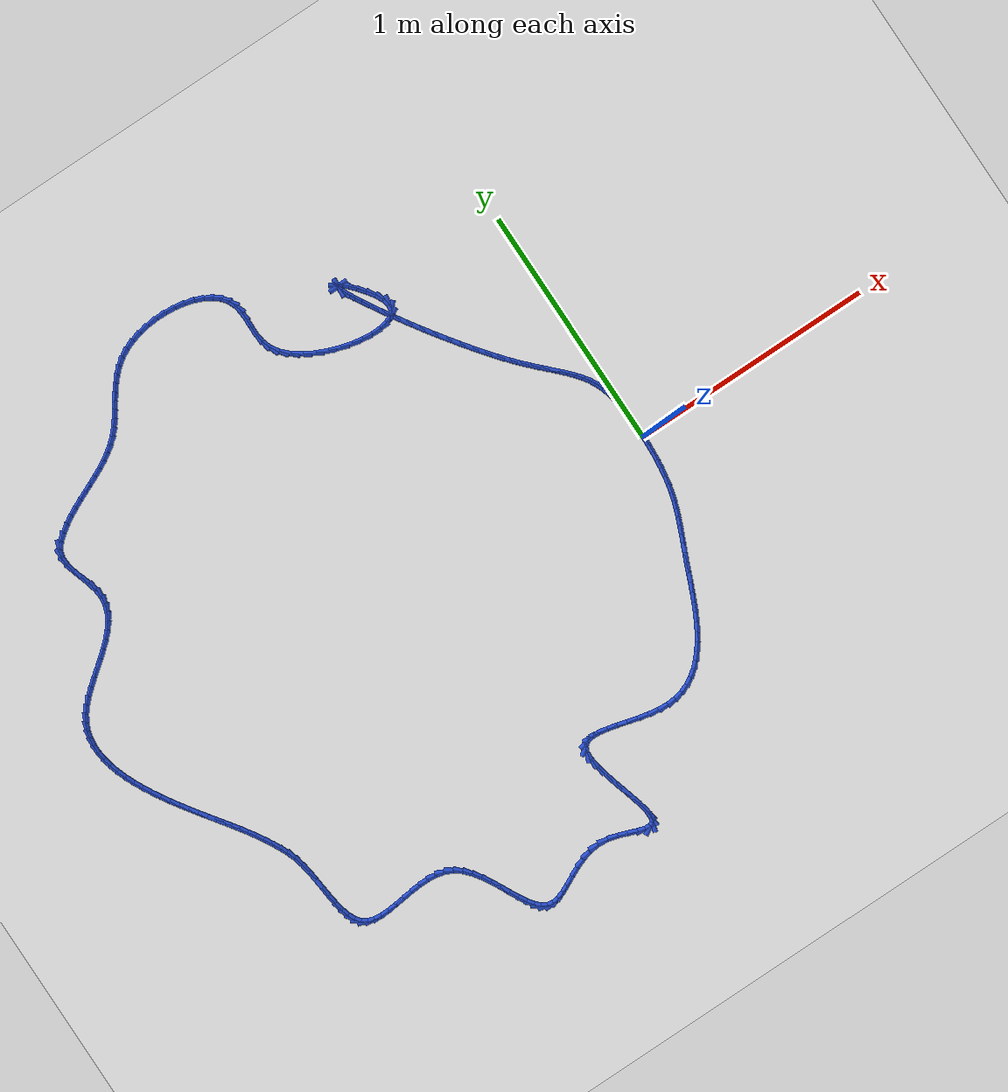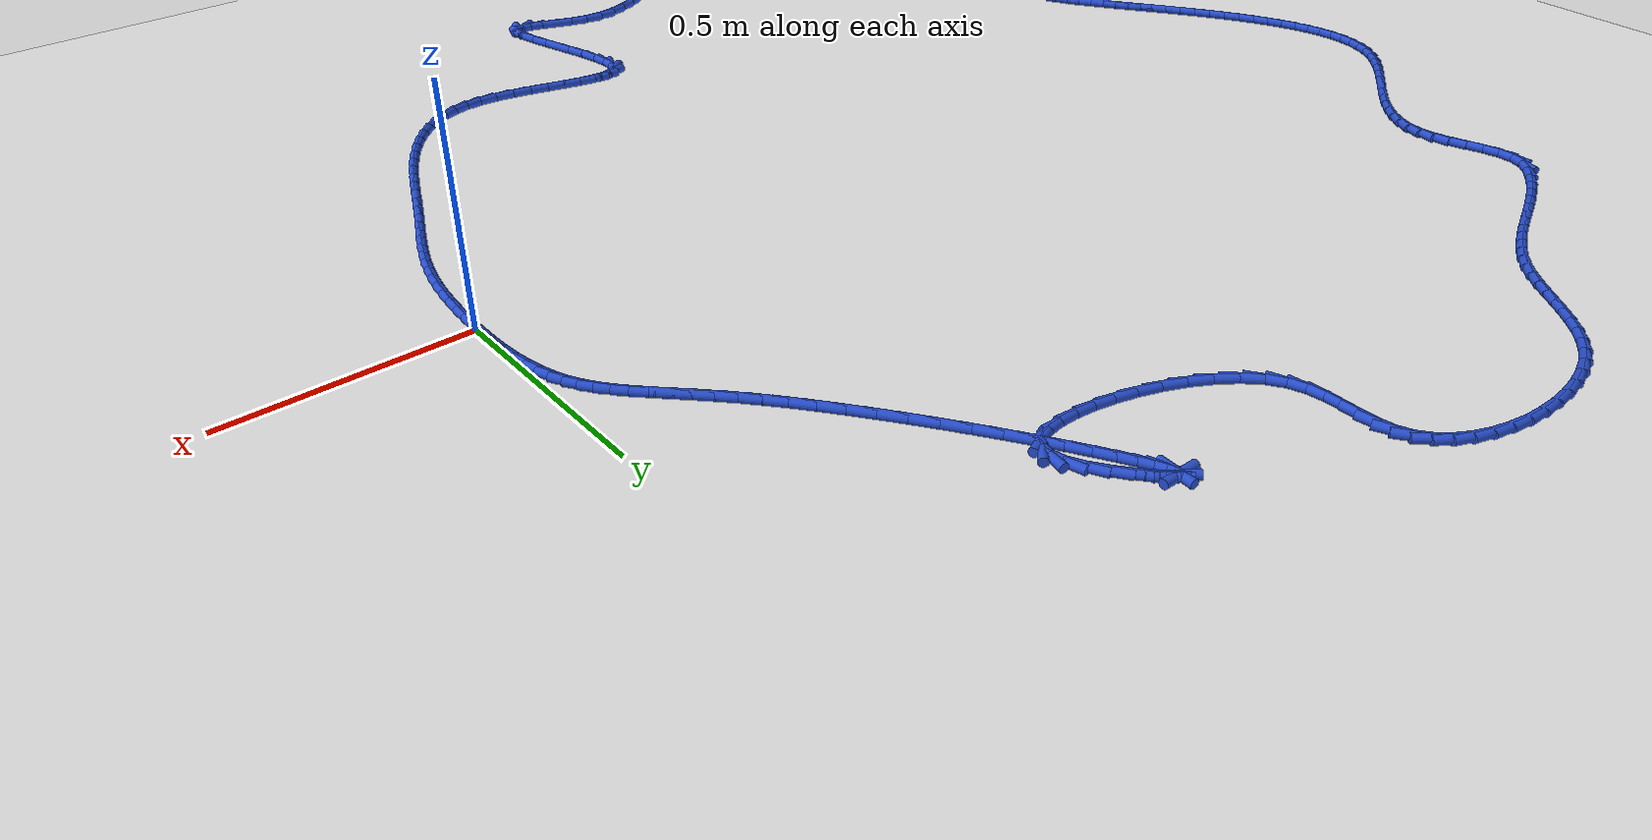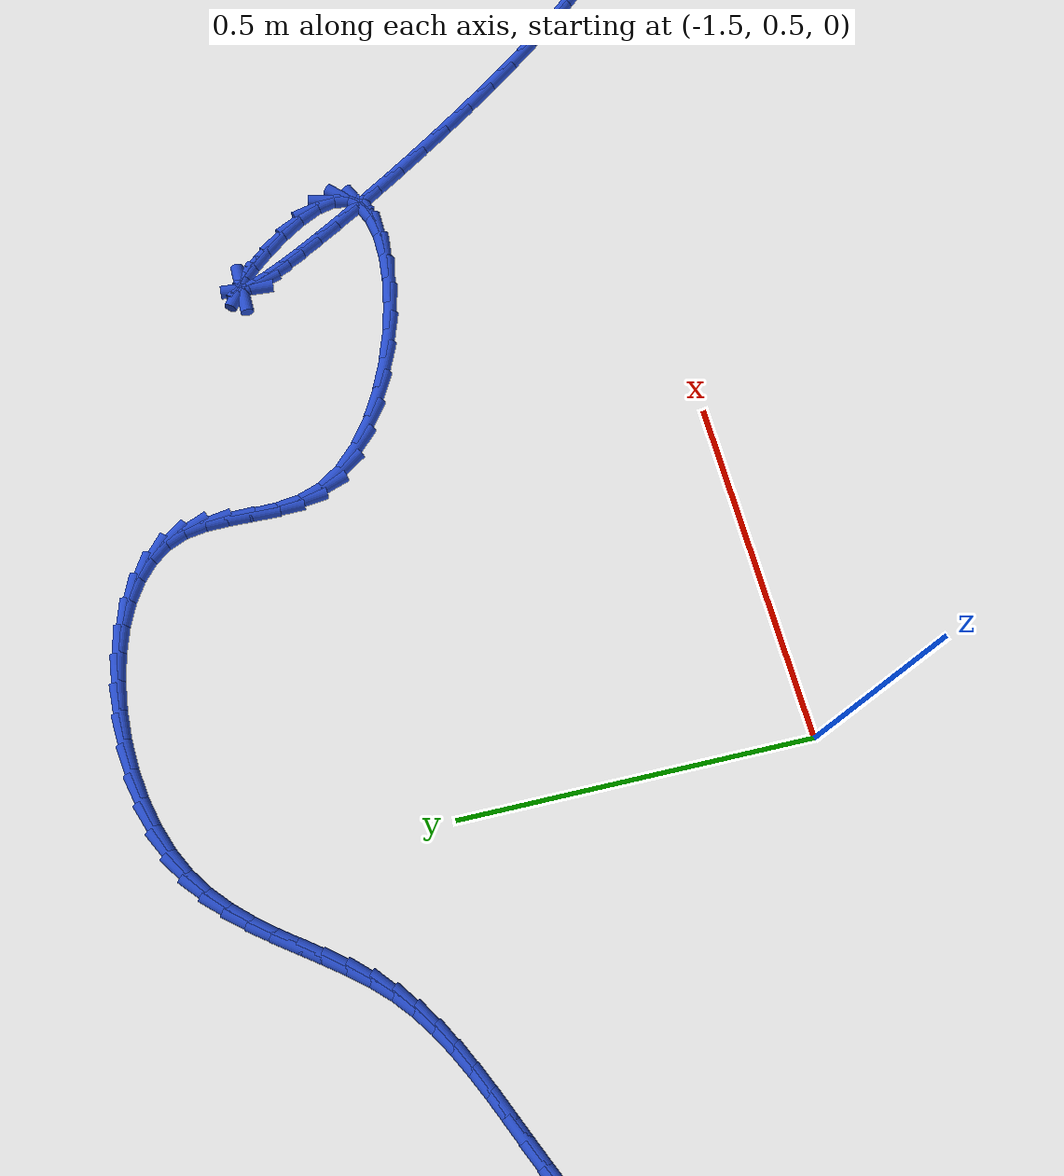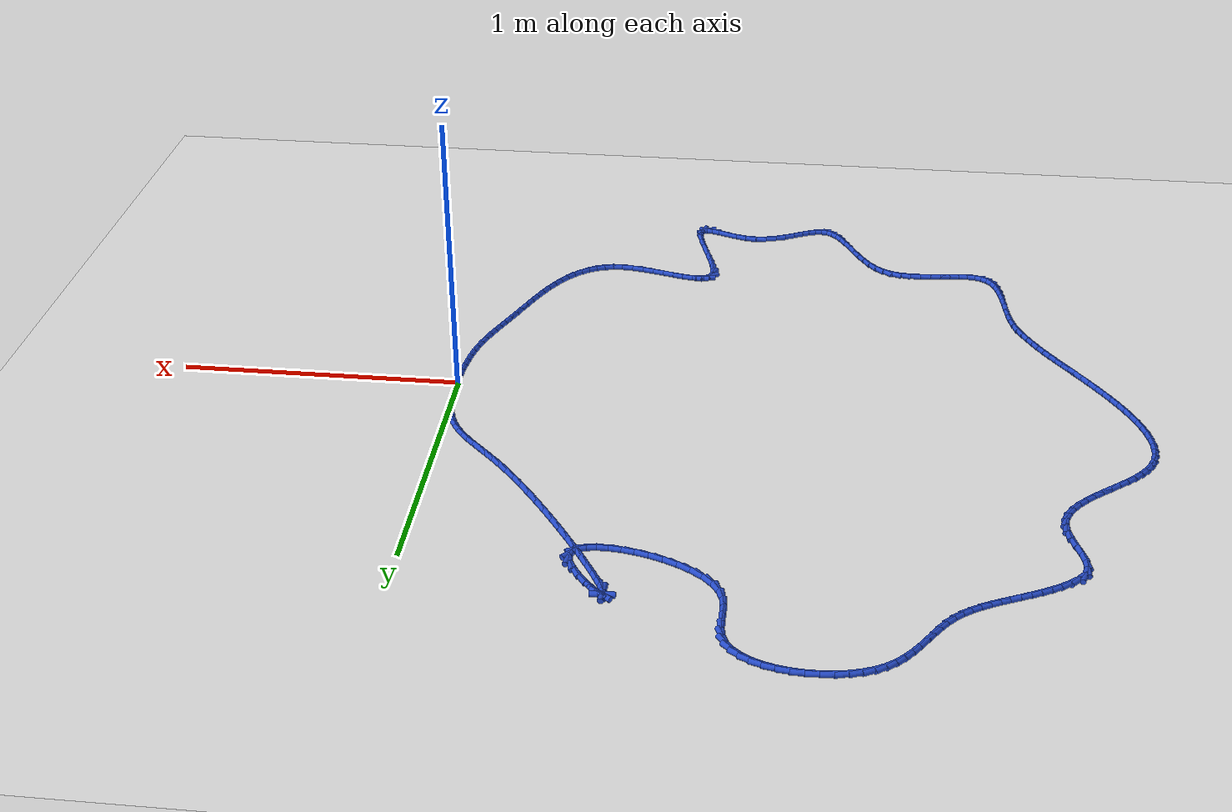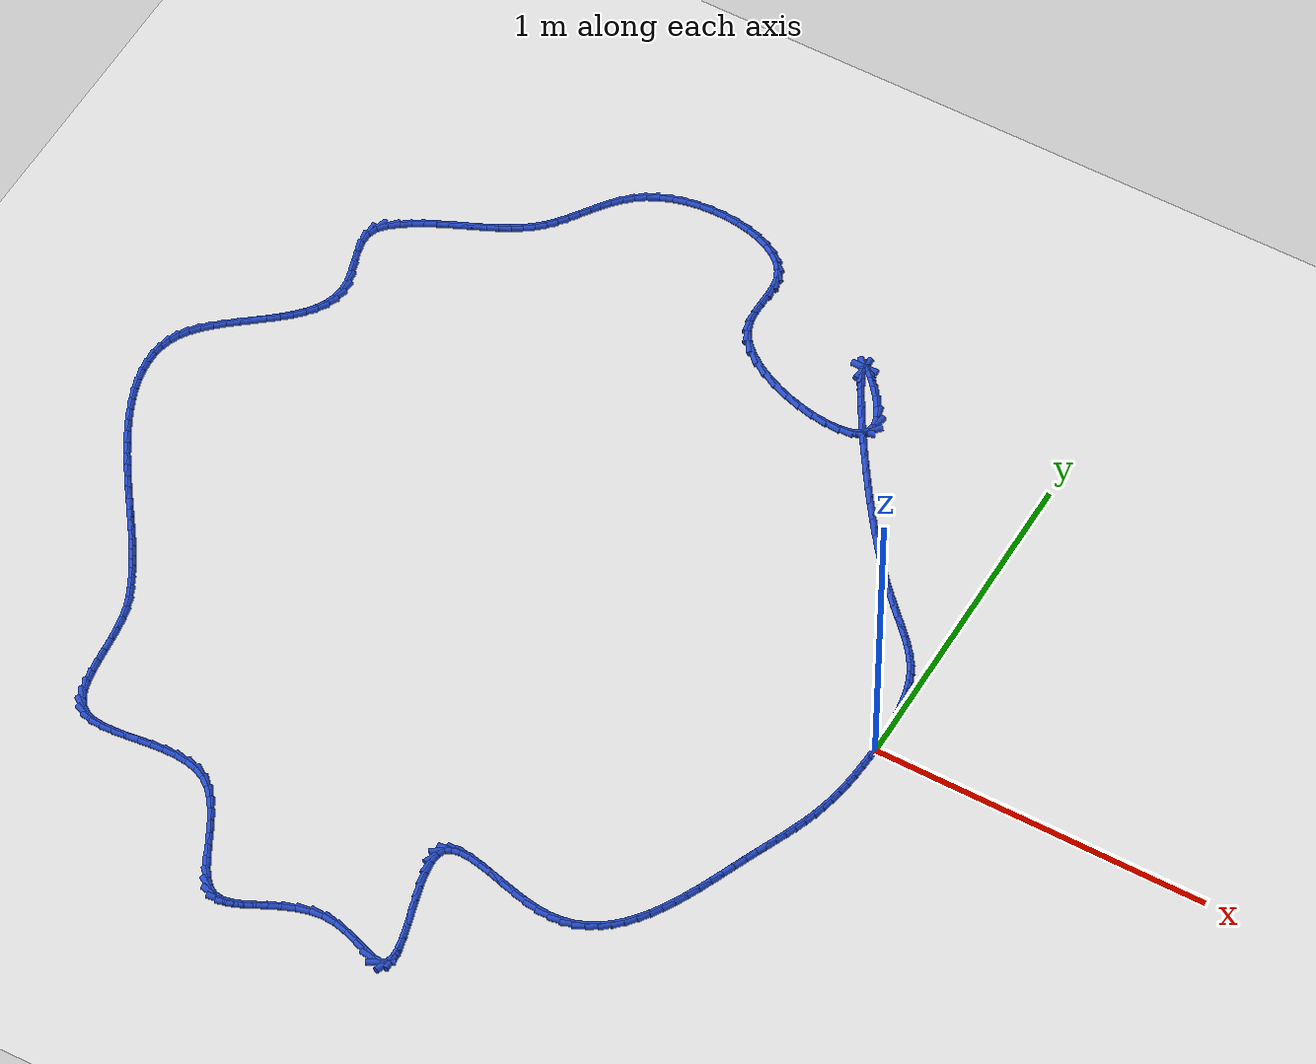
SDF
<sdf version="1.6">
 <world name="default">
  <light name="sun" type="directional">
   <pose>0 0 10 0 -0 0</pose>
   <diffuse>0.8 0.8 0.8 1</diffuse>
   <specular>0.2 0.2 0.2 1</specular>
   <attenuation>
    <range>1000</range>
    <constant>0.9</constant>
    <linear>0.01</linear>
    <quadratic>0.001</quadratic>
   </attenuation>
   <direction>-0.5 0.1 -0.9</direction>
  </light>
  <model name="ground_plane">
   <static>1</static>
   <link name="link">
    <collision name="collision">
     <geometry><plane><normal>0 0 1</normal><size>100 100</size></plane></geometry>
     <surface><friction><ode><mu>100</mu><mu2>50</mu2></ode></friction></surface>
    </collision>
    <visual name="visual">
     <cast_shadows>0</cast_shadows>
     <geometry><plane><normal>0 0 1</normal><size>100 100</size></plane></geometry>
     <material>
      <script><uri>file://media/materials/scripts/gazebo.material</uri><name>Gazebo/WhiteGlow</name></script>
     </material>
    </visual>
   </link>
  </model>
  <gravity>0 0 -9.8</gravity>
  <magnetic_field>6e-06 2.3e-05 -4.2e-05</magnetic_field>
  <atmosphere type="adiabatic"/>
  <physics name="default_physics" default="0" type="ode">
   <max_step_size>0.001</max_step_size>
   <real_time_factor>1</real_time_factor>
   <real_time_update_rate>1000</real_time_update_rate>
  </physics>
  <scene><ambient>0.4 0.4 0.4 1</ambient><background>0.7 0.7 0.7 1</background><shadows>1</shadows></scene>
  <spherical_coordinates>
   <surface_model>EARTH_WGS84</surface_model>
   <latitude_deg>0</latitude_deg>
   <longitude_deg>0</longitude_deg>
   <elevation>0</elevation>
   <heading_deg>0</heading_deg>
  </spherical_coordinates>
  <model name="line">
   <link name="link_0">
    <pose>1.6696713456276768e-17 -4.85722573273506e-17 0.01 0 1.57 1.5651949544674577</pose>
    <collision name="collision">
     <geometry><cylinder><radius>0.01</radius><length>0.08</length></cylinder></geometry>
    </collision>
    <visual name="visual">
     <material>
      <script><name>Gazebo/Blue</name><uri>file://media/materials/scripts/gazebo.material</uri></script>
     </material>
     <geometry><cylinder><radius>0.01</radius><length>0.08</length></cylinder></geometry>
    </visual>
   </link>
   <link name="link_1">
    <pose>0.00020154477289173 0.03598094417909356 0.01 0 1.57 -1.5489126024037094</pose>
    <collision name="collision">
     <geometry><cylinder><radius>0.01</radius><length>0.08</length></cylinder></geometry>
    </collision>
    <visual name="visual">
     <material>
      <script><name>Gazebo/Blue</name><uri>file://media/materials/scripts/gazebo.material</uri></script>
     </material>
     <geometry><cylinder><radius>0.01</radius><length>0.08</length></cylinder></geometry>
    </visual>
   </link>
   <link name="link_2">
    <pose>-0.0005873252235443653 0.07202344083343072 0.01 0 1.57 -1.514280589093293</pose>
    <collision name="collision">
     <geometry><cylinder><radius>0.01</radius><length>0.08</length></cylinder></geometry>
    </collision>
    <visual name="visual">
     <material>
      <script><name>Gazebo/Blue</name><uri>file://media/materials/scripts/gazebo.material</uri></script>
     </material>
     <geometry><cylinder><radius>0.01</radius><length>0.08</length></cylinder></geometry>
    </visual>
   </link>
   <link name="link_3">
    <pose>-0.002607348114027349 0.10772804001505965 0.01 0 1.57 -1.4712639073552192</pose>
    <collision name="collision">
     <geometry><cylinder><radius>0.01</radius><length>0.08</length></cylinder></geometry>
    </collision>
    <visual name="visual">
     <material>
      <script><name>Gazebo/Blue</name><uri>file://media/materials/scripts/gazebo.material</uri></script>
     </material>
     <geometry><cylinder><radius>0.01</radius><length>0.08</length></cylinder></geometry>
    </visual>
   </link>
   <link name="link_4">
    <pose>-0.0060992620232763 0.14269529177602844 0.01 0 1.57 -1.4181511056378888</pose>
    <collision name="collision">
     <geometry><cylinder><radius>0.01</radius><length>0.08</length></cylinder></geometry>
    </collision>
    <visual name="visual">
     <material>
      <script><name>Gazebo/Blue</name><uri>file://media/materials/scripts/gazebo.material</uri></script>
     </material>
     <geometry><cylinder><radius>0.01</radius><length>0.08</length></cylinder></geometry>
    </visual>
   </link>
   <link name="link_5">
    <pose>-0.011303805076010302 0.17652574616838534 0.01 0 1.57 -1.3526757125911815</pose>
    <collision name="collision">
     <geometry><cylinder><radius>0.01</radius><length>0.08</length></cylinder></geometry>
    </collision>
    <visual name="visual">
     <material>
      <script><name>Gazebo/Blue</name><uri>file://media/materials/scripts/gazebo.material</uri></script>
     </material>
     <geometry><cylinder><radius>0.01</radius><length>0.08</length></cylinder></geometry>
    </visual>
   </link>
   <link name="link_6">
    <pose>-0.018461715396948433 0.20881995324417854 0.01 0 1.57 -1.2719683618093642</pose>
    <collision name="collision">
     <geometry><cylinder><radius>0.01</radius><length>0.08</length></cylinder></geometry>
    </collision>
    <visual name="visual">
     <material>
      <script><name>Gazebo/Blue</name><uri>file://media/materials/scripts/gazebo.material</uri></script>
     </material>
     <geometry><cylinder><radius>0.01</radius><length>0.08</length></cylinder></geometry>
    </visual>
   </link>
   <link name="link_7">
    <pose>-0.02781373111080977 0.23917846305545604 0.01 0 1.57 -1.173853776356065</pose>
    <collision name="collision">
     <geometry><cylinder><radius>0.01</radius><length>0.08</length></cylinder></geometry>
    </collision>
    <visual name="visual">
     <material>
      <script><name>Gazebo/Blue</name><uri>file://media/materials/scripts/gazebo.material</uri></script>
     </material>
     <geometry><cylinder><radius>0.01</radius><length>0.08</length></cylinder></geometry>
    </visual>
   </link>
   <link name="link_8">
    <pose>-0.03958216443736759 0.2672524257600745 0.01 0 1.57 -1.0713666835665674</pose>
    <collision name="collision">
     <geometry><cylinder><radius>0.01</radius><length>0.08</length></cylinder></geometry>
    </collision>
    <visual name="visual">
     <material>
      <script><name>Gazebo/Blue</name><uri>file://media/materials/scripts/gazebo.material</uri></script>
     </material>
     <geometry><cylinder><radius>0.01</radius><length>0.08</length></cylinder></geometry>
    </visual>
   </link>
   <link name="link_9">
    <pose>-0.05377807319103435 0.2932731255877425 0.01 0 1.57 -0.9794179680638049</pose>
    <collision name="collision">
     <geometry><cylinder><radius>0.01</radius><length>0.08</length></cylinder></geometry>
    </collision>
    <visual name="visual">
     <material>
      <script><name>Gazebo/Blue</name><uri>file://media/materials/scripts/gazebo.material</uri></script>
     </material>
     <geometry><cylinder><radius>0.01</radius><length>0.08</length></cylinder></geometry>
    </visual>
   </link>
   <link name="link_10">
    <pose>-0.0702776083239604 0.31784231983447486 0.01 0 1.57 -0.9038974325339743</pose>
    <collision name="collision">
     <geometry><cylinder><radius>0.01</radius><length>0.08</length></cylinder></geometry>
    </collision>
    <visual name="visual">
     <material>
      <script><name>Gazebo/Blue</name><uri>file://media/materials/scripts/gazebo.material</uri></script>
     </material>
     <geometry><cylinder><radius>0.01</radius><length>0.08</length></cylinder></geometry>
    </visual>
   </link>
   <link name="link_11">
    <pose>-0.08895473381124924 0.34156777154039003 0.01 0 1.57 -0.8477529484330161</pose>
    <collision name="collision">
     <geometry><cylinder><radius>0.01</radius><length>0.08</length></cylinder></geometry>
    </collision>
    <visual name="visual">
     <material>
      <script><name>Gazebo/Blue</name><uri>file://media/materials/scripts/gazebo.material</uri></script>
     </material>
     <geometry><cylinder><radius>0.01</radius><length>0.08</length></cylinder></geometry>
    </visual>
   </link>
   <link name="link_12">
    <pose>-0.10968341362800438 0.36505724374560633 0.01 0 1.57 -0.8113419454200357</pose>
    <collision name="collision">
     <geometry><cylinder><radius>0.01</radius><length>0.08</length></cylinder></geometry>
    </collision>
    <visual name="visual">
     <material>
      <script><name>Gazebo/Blue</name><uri>file://media/materials/scripts/gazebo.material</uri></script>
     </material>
     <geometry><cylinder><radius>0.01</radius><length>0.08</length></cylinder></geometry>
    </visual>
   </link>
   <link name="link_13">
    <pose>-0.1323376117493292 0.3889184994902424 0.01 0 1.57 -0.7932512524994244</pose>
    <collision name="collision">
     <geometry><cylinder><radius>0.01</radius><length>0.08</length></cylinder></geometry>
    </collision>
    <visual name="visual">
     <material>
      <script><name>Gazebo/Blue</name><uri>file://media/materials/scripts/gazebo.material</uri></script>
     </material>
     <geometry><cylinder><radius>0.01</radius><length>0.08</length></cylinder></geometry>
    </visual>
   </link>
   <link name="link_14">
    <pose>-0.1567912921503271 0.41375930181441606 0.01 0 1.57 -0.7911251281203546</pose>
    <collision name="collision">
     <geometry><cylinder><radius>0.01</radius><length>0.08</length></cylinder></geometry>
    </collision>
    <visual name="visual">
     <material>
      <script><name>Gazebo/Blue</name><uri>file://media/materials/scripts/gazebo.material</uri></script>
     </material>
     <geometry><cylinder><radius>0.01</radius><length>0.08</length></cylinder></geometry>
    </visual>
   </link>
   <link name="link_15">
    <pose>-0.18291841880610163 0.440187413758246 0.01 0 1.57 -0.8022471214272122</pose>
    <collision name="collision">
     <geometry><cylinder><radius>0.01</radius><length>0.08</length></cylinder></geometry>
    </collision>
    <visual name="visual">
     <material>
      <script><name>Gazebo/Blue</name><uri>file://media/materials/scripts/gazebo.material</uri></script>
     </material>
     <geometry><cylinder><radius>0.01</radius><length>0.08</length></cylinder></geometry>
    </visual>
   </link>
   <link name="link_16">
    <pose>-0.21059295569175626 0.4688105983618507 0.01 0 1.57 -0.8238794031601178</pose>
    <collision name="collision">
     <geometry><cylinder><radius>0.01</radius><length>0.08</length></cylinder></geometry>
    </collision>
    <visual name="visual">
     <material>
      <script><name>Gazebo/Blue</name><uri>file://media/materials/scripts/gazebo.material</uri></script>
     </material>
     <geometry><cylinder><radius>0.01</radius><length>0.08</length></cylinder></geometry>
    </visual>
   </link>
   <link name="link_17">
    <pose>-0.23968886678239443 0.5002366186653483 0.01 0 1.57 -0.8529064459018548</pose>
    <collision name="collision">
     <geometry><cylinder><radius>0.01</radius><length>0.08</length></cylinder></geometry>
    </collision>
    <visual name="visual">
     <material>
      <script><name>Gazebo/Blue</name><uri>file://media/materials/scripts/gazebo.material</uri></script>
     </material>
     <geometry><cylinder><radius>0.01</radius><length>0.08</length></cylinder></geometry>
    </visual>
   </link>
   <link name="link_18">
    <pose>-0.27007105732675757 0.5350250624790417 0.01 0 1.57 -0.8806291100988936</pose>
    <collision name="collision">
     <geometry><cylinder><radius>0.01</radius><length>0.08</length></cylinder></geometry>
    </collision>
    <visual name="visual">
     <material>
      <script><name>Gazebo/Blue</name><uri>file://media/materials/scripts/gazebo.material</uri></script>
     </material>
     <geometry><cylinder><radius>0.01</radius><length>0.08</length></cylinder></geometry>
    </visual>
   </link>
   <link name="link_19">
    <pose>-0.30147860523518016 0.5730663550066336 0.01 0 1.57 -0.9032263792399842</pose>
    <collision name="collision">
     <geometry><cylinder><radius>0.01</radius><length>0.08</length></cylinder></geometry>
    </collision>
    <visual name="visual">
     <material>
      <script><name>Gazebo/Blue</name><uri>file://media/materials/scripts/gazebo.material</uri></script>
     </material>
     <geometry><cylinder><radius>0.01</radius><length>0.08</length></cylinder></geometry>
    </visual>
   </link>
   <link name="link_20">
    <pose>-0.3335584677494666 0.6137610143501143 0.01 0 1.57 -0.9221630874930781</pose>
    <collision name="collision">
     <geometry><cylinder><radius>0.01</radius><length>0.08</length></cylinder></geometry>
    </collision>
    <visual name="visual">
     <material>
      <script><name>Gazebo/Blue</name><uri>file://media/materials/scripts/gazebo.material</uri></script>
     </material>
     <geometry><cylinder><radius>0.01</radius><length>0.08</length></cylinder></geometry>
    </visual>
   </link>
   <link name="link_21">
    <pose>-0.36595549085444545 0.6564983307317526 0.01 0 1.57 -0.9385152976863078</pose>
    <collision name="collision">
     <geometry><cylinder><radius>0.01</radius><length>0.08</length></cylinder></geometry>
    </collision>
    <visual name="visual">
     <material>
      <script><name>Gazebo/Blue</name><uri>file://media/materials/scripts/gazebo.material</uri></script>
     </material>
     <geometry><cylinder><radius>0.01</radius><length>0.08</length></cylinder></geometry>
    </visual>
   </link>
   <link name="link_22">
    <pose>-0.39831452053494515 0.7006675943738175 0.01 0 1.57 -0.9530561510162411</pose>
    <collision name="collision">
     <geometry><cylinder><radius>0.01</radius><length>0.08</length></cylinder></geometry>
    </collision>
    <visual name="visual">
     <material>
      <script><name>Gazebo/Blue</name><uri>file://media/materials/scripts/gazebo.material</uri></script>
     </material>
     <geometry><cylinder><radius>0.01</radius><length>0.08</length></cylinder></geometry>
    </visual>
   </link>
   <link name="link_23">
    <pose>-0.43028040277579416 0.7456580954985781 0.01 0 1.57 -0.9663807685283005</pose>
    <collision name="collision">
     <geometry><cylinder><radius>0.01</radius><length>0.08</length></cylinder></geometry>
    </collision>
    <visual name="visual">
     <material>
      <script><name>Gazebo/Blue</name><uri>file://media/materials/scripts/gazebo.material</uri></script>
     </material>
     <geometry><cylinder><radius>0.01</radius><length>0.08</length></cylinder></geometry>
    </visual>
   </link>
   <link name="link_24">
    <pose>-0.46149798356182087 0.7908591243283036 0.01 0 1.57 -0.9789881647580871</pose>
    <collision name="collision">
     <geometry><cylinder><radius>0.01</radius><length>0.08</length></cylinder></geometry>
    </collision>
    <visual name="visual">
     <material>
      <script><name>Gazebo/Blue</name><uri>file://media/materials/scripts/gazebo.material</uri></script>
     </material>
     <geometry><cylinder><radius>0.01</radius><length>0.08</length></cylinder></geometry>
    </visual>
   </link>
   <link name="link_25">
    <pose>-0.49161210887785384 0.8356599710852626 0.01 0 1.57 -0.9913442603315072</pose>
    <collision name="collision">
     <geometry><cylinder><radius>0.01</radius><length>0.08</length></cylinder></geometry>
    </collision>
    <visual name="visual">
     <material>
      <script><name>Gazebo/Blue</name><uri>file://media/materials/scripts/gazebo.material</uri></script>
     </material>
     <geometry><cylinder><radius>0.01</radius><length>0.08</length></cylinder></geometry>
    </visual>
   </link>
   <link name="link_26">
    <pose>-0.5202676247087217 0.8794499259917243 0.01 0 1.57 -1.003943130118687</pose>
    <collision name="collision">
     <geometry><cylinder><radius>0.01</radius><length>0.08</length></cylinder></geometry>
    </collision>
    <visual name="visual">
     <material>
      <script><name>Gazebo/Blue</name><uri>file://media/materials/scripts/gazebo.material</uri></script>
     </material>
     <geometry><cylinder><radius>0.01</radius><length>0.08</length></cylinder></geometry>
    </visual>
   </link>
   <link name="link_27">
    <pose>-0.5471093770392523 0.9216182792699575 0.01 0 1.57 -1.0173849920575084</pose>
    <collision name="collision">
     <geometry><cylinder><radius>0.01</radius><length>0.08</length></cylinder></geometry>
    </collision>
    <visual name="visual">
     <material>
      <script><name>Gazebo/Blue</name><uri>file://media/materials/scripts/gazebo.material</uri></script>
     </material>
     <geometry><cylinder><radius>0.01</radius><length>0.08</length></cylinder></geometry>
    </visual>
   </link>
   <link name="link_28">
    <pose>-0.5717822118542749 0.9615543211422319 0.01 0 1.57 -1.0325015610652137</pose>
    <collision name="collision">
     <geometry><cylinder><radius>0.01</radius><length>0.08</length></cylinder></geometry>
    </collision>
    <visual name="visual">
     <material>
      <script><name>Gazebo/Blue</name><uri>file://media/materials/scripts/gazebo.material</uri></script>
     </material>
     <geometry><cylinder><radius>0.01</radius><length>0.08</length></cylinder></geometry>
    </visual>
   </link>
   <link name="link_29">
    <pose>-0.5939309751386179 0.9986473418308162 0.01 0 1.57 -1.0505956555619034</pose>
    <collision name="collision">
     <geometry><cylinder><radius>0.01</radius><length>0.08</length></cylinder></geometry>
    </collision>
    <visual name="visual">
     <material>
      <script><name>Gazebo/Blue</name><uri>file://media/materials/scripts/gazebo.material</uri></script>
     </material>
     <geometry><cylinder><radius>0.01</radius><length>0.08</length></cylinder></geometry>
    </visual>
   </link>
   <link name="link_30">
    <pose>-0.6132005128771093 1.032286631557979 0.01 0 1.57 -1.0739698075209996</pose>
    <collision name="collision">
     <geometry><cylinder><radius>0.01</radius><length>0.08</length></cylinder></geometry>
    </collision>
    <visual name="visual">
     <material>
      <script><name>Gazebo/Blue</name><uri>file://media/materials/scripts/gazebo.material</uri></script>
     </material>
     <geometry><cylinder><radius>0.01</radius><length>0.08</length></cylinder></geometry>
    </visual>
   </link>
   <link name="link_31">
    <pose>-0.6292356710545778 1.0618614805459898 0.01 0 1.57 -1.1072844598714207</pose>
    <collision name="collision">
     <geometry><cylinder><radius>0.01</radius><length>0.08</length></cylinder></geometry>
    </collision>
    <visual name="visual">
     <material>
      <script><name>Gazebo/Blue</name><uri>file://media/materials/scripts/gazebo.material</uri></script>
     </material>
     <geometry><cylinder><radius>0.01</radius><length>0.08</length></cylinder></geometry>
    </visual>
   </link>
   <link name="link_32">
    <pose>-0.6416812956558517 1.0867611790171174 0.01 0 1.57 -1.1618195149888566</pose>
    <collision name="collision">
     <geometry><cylinder><radius>0.01</radius><length>0.08</length></cylinder></geometry>
    </collision>
    <visual name="visual">
     <material>
      <script><name>Gazebo/Blue</name><uri>file://media/materials/scripts/gazebo.material</uri></script>
     </material>
     <geometry><cylinder><radius>0.01</radius><length>0.08</length></cylinder></geometry>
    </visual>
   </link>
   <link name="link_33">
    <pose>-0.6501822326657599 1.1063750171936308 0.01 0 1.57 -1.2736033630644181</pose>
    <collision name="collision">
     <geometry><cylinder><radius>0.01</radius><length>0.08</length></cylinder></geometry>
    </collision>
    <visual name="visual">
     <material>
      <script><name>Gazebo/Blue</name><uri>file://media/materials/scripts/gazebo.material</uri></script>
     </material>
     <geometry><cylinder><radius>0.01</radius><length>0.08</length></cylinder></geometry>
    </visual>
   </link>
   <link name="link_34">
    <pose>-0.6543833280691305 1.120092285297799 0.01 0 1.57 1.5079249345035188</pose>
    <collision name="collision">
     <geometry><cylinder><radius>0.01</radius><length>0.08</length></cylinder></geometry>
    </collision>
    <visual name="visual">
     <material>
      <script><name>Gazebo/Blue</name><uri>file://media/materials/scripts/gazebo.material</uri></script>
     </material>
     <geometry><cylinder><radius>0.01</radius><length>0.08</length></cylinder></geometry>
    </visual>
   </link>
   <link name="link_35">
    <pose>-0.6539294278507919 1.127302273551891 0.01 0 1.57 0.01683548589873867</pose>
    <collision name="collision">
     <geometry><cylinder><radius>0.01</radius><length>0.08</length></cylinder></geometry>
    </collision>
    <visual name="visual">
     <material>
      <script><name>Gazebo/Blue</name><uri>file://media/materials/scripts/gazebo.material</uri></script>
     </material>
     <geometry><cylinder><radius>0.01</radius><length>0.08</length></cylinder></geometry>
    </visual>
   </link>
   <link name="link_36">
    <pose>-0.6484653779955731 1.1273942721781762 0.01 0 1.57 -0.6141975529916798</pose>
    <collision name="collision">
     <geometry><cylinder><radius>0.01</radius><length>0.08</length></cylinder></geometry>
    </collision>
    <visual name="visual">
     <material>
      <script><name>Gazebo/Blue</name><uri>file://media/materials/scripts/gazebo.material</uri></script>
     </material>
     <geometry><cylinder><radius>0.01</radius><length>0.08</length></cylinder></geometry>
    </visual>
   </link>
   <link name="link_37">
    <pose>-0.6376360244883023 1.1197575713989232 0.01 0 1.57 -0.7677654376215126</pose>
    <collision name="collision">
     <geometry><cylinder><radius>0.01</radius><length>0.08</length></cylinder></geometry>
    </collision>
    <visual name="visual">
     <material>
      <script><name>Gazebo/Blue</name><uri>file://media/materials/scripts/gazebo.material</uri></script>
     </material>
     <geometry><cylinder><radius>0.01</radius><length>0.08</length></cylinder></geometry>
    </visual>
   </link>
   <link name="link_38">
    <pose>-0.6210878179454563 1.1037828914354766 0.01 0 1.57 -0.8380251424405725</pose>
    <collision name="collision">
     <geometry><cylinder><radius>0.01</radius><length>0.08</length></cylinder></geometry>
    </collision>
    <visual name="visual">
     <material>
      <script><name>Gazebo/Blue</name><uri>file://media/materials/scripts/gazebo.material</uri></script>
     </material>
     <geometry><cylinder><radius>0.01</radius><length>0.08</length></cylinder></geometry>
    </visual>
   </link>
   <link name="link_39">
    <pose>-0.5994410840275702 1.0797288404220173 0.01 0 1.57 -0.8987101870398445</pose>
    <collision name="collision">
     <geometry><cylinder><radius>0.01</radius><length>0.08</length></cylinder></geometry>
    </collision>
    <visual name="visual">
     <material>
      <script><name>Gazebo/Blue</name><uri>file://media/materials/scripts/gazebo.material</uri></script>
     </material>
     <geometry><cylinder><radius>0.01</radius><length>0.08</length></cylinder></geometry>
    </visual>
   </link>
   <link name="link_40">
    <pose>-0.5759406756607088 1.0501929256200482 0.01 0 1.57 -0.9759502711572631</pose>
    <collision name="collision">
     <geometry><cylinder><radius>0.01</radius><length>0.08</length></cylinder></geometry>
    </collision>
    <visual name="visual">
     <material>
      <script><name>Gazebo/Blue</name><uri>file://media/materials/scripts/gazebo.material</uri></script>
     </material>
     <geometry><cylinder><radius>0.01</radius><length>0.08</length></cylinder></geometry>
    </visual>
   </link>
   <link name="link_41">
    <pose>-0.554269107272415 1.0181626849519487 0.01 0 1.57 -1.097261912312723</pose>
    <collision name="collision">
     <geometry><cylinder><radius>0.01</radius><length>0.08</length></cylinder></geometry>
    </collision>
    <visual name="visual">
     <material>
      <script><name>Gazebo/Blue</name><uri>file://media/materials/scripts/gazebo.material</uri></script>
     </material>
     <geometry><cylinder><radius>0.01</radius><length>0.08</length></cylinder></geometry>
    </visual>
   </link>
   <link name="link_42">
    <pose>-0.5381088932902319 0.9866256563401004 0.01 0 1.57 -1.3273937072860282</pose>
    <collision name="collision">
     <geometry><cylinder><radius>0.01</radius><length>0.08</length></cylinder></geometry>
    </collision>
    <visual name="visual">
     <material>
      <script><name>Gazebo/Blue</name><uri>file://media/materials/scripts/gazebo.material</uri></script>
     </material>
     <geometry><cylinder><radius>0.01</radius><length>0.08</length></cylinder></geometry>
    </visual>
   </link>
   <link name="link_43">
    <pose>-0.5311416479299992 0.9585688188624538 0.01 0 1.57 1.3614976762369895</pose>
    <collision name="collision">
     <geometry><cylinder><radius>0.01</radius><length>0.08</length></cylinder></geometry>
    </collision>
    <visual name="visual">
     <material>
      <script><name>Gazebo/Blue</name><uri>file://media/materials/scripts/gazebo.material</uri></script>
     </material>
     <geometry><cylinder><radius>0.01</radius><length>0.08</length></cylinder></geometry>
    </visual>
   </link>
   <link name="link_44">
    <pose>-0.5358814487536512 0.9362543539146444 0.01 0 1.57 0.8153649722992526</pose>
    <collision name="collision">
     <geometry><cylinder><radius>0.01</radius><length>0.08</length></cylinder></geometry>
    </collision>
    <visual name="visual">
     <material>
      <script><name>Gazebo/Blue</name><uri>file://media/materials/scripts/gazebo.material</uri></script>
     </material>
     <geometry><cylinder><radius>0.01</radius><length>0.08</length></cylinder></geometry>
    </visual>
   </link>
   <link name="link_45">
    <pose>-0.551381722794714 0.9197960979355111 0.01 0 1.57 0.41542155542267994</pose>
    <collision name="collision">
     <geometry><cylinder><radius>0.01</radius><length>0.08</length></cylinder></geometry>
    </collision>
    <visual name="visual">
     <material>
      <script><name>Gazebo/Blue</name><uri>file://media/materials/scripts/gazebo.material</uri></script>
     </material>
     <geometry><cylinder><radius>0.01</radius><length>0.08</length></cylinder></geometry>
    </visual>
   </link>
   <link name="link_46">
    <pose>-0.5760577162157029 0.9089117096382022 0.01 0 1.57 0.1716257320462816</pose>
    <collision name="collision">
     <geometry><cylinder><radius>0.01</radius><length>0.08</length></cylinder></geometry>
    </collision>
    <visual name="visual">
     <material>
      <script><name>Gazebo/Blue</name><uri>file://media/materials/scripts/gazebo.material</uri></script>
     </material>
     <geometry><cylinder><radius>0.01</radius><length>0.08</length></cylinder></geometry>
    </visual>
   </link>
   <link name="link_47">
    <pose>-0.6083246751791332 0.903318847735865 0.01 0 1.57 0.015249103785514572</pose>
    <collision name="collision">
     <geometry><cylinder><radius>0.01</radius><length>0.08</length></cylinder></geometry>
    </collision>
    <visual name="visual">
     <material>
      <script><name>Gazebo/Blue</name><uri>file://media/materials/scripts/gazebo.material</uri></script>
     </material>
     <geometry><cylinder><radius>0.01</radius><length>0.08</length></cylinder></geometry>
    </visual>
   </link>
   <link name="link_48">
    <pose>-0.6465978458475204 0.9027351709416472 0.01 0 1.57 -0.09673897131933525</pose>
    <collision name="collision">
     <geometry><cylinder><radius>0.01</radius><length>0.08</length></cylinder></geometry>
    </collision>
    <visual name="visual">
     <material>
      <script><name>Gazebo/Blue</name><uri>file://media/materials/scripts/gazebo.material</uri></script>
     </material>
     <geometry><cylinder><radius>0.01</radius><length>0.08</length></cylinder></geometry>
    </visual>
   </link>
   <link name="link_49">
    <pose>-0.6892924743833799 0.9068783379686965 0.01 0 1.57 -0.18642014039910562</pose>
    <collision name="collision">
     <geometry><cylinder><radius>0.01</radius><length>0.08</length></cylinder></geometry>
    </collision>
    <visual name="visual">
     <material>
      <script><name>Gazebo/Blue</name><uri>file://media/materials/scripts/gazebo.material</uri></script>
     </material>
     <geometry><cylinder><radius>0.01</radius><length>0.08</length></cylinder></geometry>
    </visual>
   </link>
   <link name="link_50">
    <pose>-0.7348238069492272 0.9154660075301603 0.01 0 1.57 -0.2660680815209938</pose>
    <collision name="collision">
     <geometry><cylinder><radius>0.01</radius><length>0.08</length></cylinder></geometry>
    </collision>
    <visual name="visual">
     <material>
      <script><name>Gazebo/Blue</name><uri>file://media/materials/scripts/gazebo.material</uri></script>
     </material>
     <geometry><cylinder><radius>0.01</radius><length>0.08</length></cylinder></geometry>
    </visual>
   </link>
   <link name="link_51">
    <pose>-0.7816070897075779 0.9282158383391869 0.01 0 1.57 -0.34379115194512244</pose>
    <collision name="collision">
     <geometry><cylinder><radius>0.01</radius><length>0.08</length></cylinder></geometry>
    </collision>
    <visual name="visual">
     <material>
      <script><name>Gazebo/Blue</name><uri>file://media/materials/scripts/gazebo.material</uri></script>
     </material>
     <geometry><cylinder><radius>0.01</radius><length>0.08</length></cylinder></geometry>
    </visual>
   </link>
   <link name="link_52">
    <pose>-0.8280575688209469 0.9448454891089232 0.01 0 1.57 -0.42634630041385174</pose>
    <collision name="collision">
     <geometry><cylinder><radius>0.01</radius><length>0.08</length></cylinder></geometry>
    </collision>
    <visual name="visual">
     <material>
      <script><name>Gazebo/Blue</name><uri>file://media/materials/scripts/gazebo.material</uri></script>
     </material>
     <geometry><cylinder><radius>0.01</radius><length>0.08</length></cylinder></geometry>
    </visual>
   </link>
   <link name="link_53">
    <pose>-0.8725904904518501 0.9650726185525174 0.01 0 1.57 -0.5209118596285488</pose>
    <collision name="collision">
     <geometry><cylinder><radius>0.01</radius><length>0.08</length></cylinder></geometry>
    </collision>
    <visual name="visual">
     <material>
      <script><name>Gazebo/Blue</name><uri>file://media/materials/scripts/gazebo.material</uri></script>
     </material>
     <geometry><cylinder><radius>0.01</radius><length>0.08</length></cylinder></geometry>
    </visual>
   </link>
   <link name="link_54">
    <pose>-0.9136211007628028 0.9886148853831167 0.01 0 1.57 -0.6366538419568947</pose>
    <collision name="collision">
     <geometry><cylinder><radius>0.01</radius><length>0.08</length></cylinder></geometry>
    </collision>
    <visual name="visual">
     <material>
      <script><name>Gazebo/Blue</name><uri>file://media/materials/scripts/gazebo.material</uri></script>
     </material>
     <geometry><cylinder><radius>0.01</radius><length>0.08</length></cylinder></geometry>
    </visual>
   </link>
   <link name="link_55">
    <pose>-0.9495646459163204 1.0151899483138689 0.01 0 1.57 -0.7863161514590385</pose>
    <collision name="collision">
     <geometry><cylinder><radius>0.01</radius><length>0.08</length></cylinder></geometry>
    </collision>
    <visual name="visual">
     <material>
      <script><name>Gazebo/Blue</name><uri>file://media/materials/scripts/gazebo.material</uri></script>
     </material>
     <geometry><cylinder><radius>0.01</radius><length>0.08</length></cylinder></geometry>
    </visual>
   </link>
   <link name="link_56">
    <pose>-0.9788363720749184 1.0445154660579217 0.01 0 1.57 -0.9867366314882391</pose>
    <collision name="collision">
     <geometry><cylinder><radius>0.01</radius><length>0.08</length></cylinder></geometry>
    </collision>
    <visual name="visual">
     <material>
      <script><name>Gazebo/Blue</name><uri>file://media/materials/scripts/gazebo.material</uri></script>
     </material>
     <geometry><cylinder><radius>0.01</radius><length>0.08</length></cylinder></geometry>
    </visual>
   </link>
   <link name="link_57">
    <pose>-0.9998515254011121 1.0763090973284228 0.01 0 1.57 -1.2338779355242624</pose>
    <collision name="collision">
     <geometry><cylinder><radius>0.01</radius><length>0.08</length></cylinder></geometry>
    </collision>
    <visual name="visual">
     <material>
      <script><name>Gazebo/Blue</name><uri>file://media/materials/scripts/gazebo.material</uri></script>
     </material>
     <geometry><cylinder><radius>0.01</radius><length>0.08</length></cylinder></geometry>
    </visual>
   </link>
   <link name="link_58">
    <pose>-1.011719207614011 1.1101902915701518 0.01 0 1.57 -1.4353762513213302</pose>
    <collision name="collision">
     <geometry><cylinder><radius>0.01</radius><length>0.08</length></cylinder></geometry>
    </collision>
    <visual name="visual">
     <material>
      <script><name>Gazebo/Blue</name><uri>file://media/materials/scripts/gazebo.material</uri></script>
     </material>
     <geometry><cylinder><radius>0.01</radius><length>0.08</length></cylinder></geometry>
    </visual>
   </link>
   <link name="link_59">
    <pose>-1.0165111078393867 1.1453591695377592 0.01 0 1.57 -1.554526504624535</pose>
    <collision name="collision">
     <geometry><cylinder><radius>0.01</radius><length>0.08</length></cylinder></geometry>
    </collision>
    <visual name="visual">
     <material>
      <script><name>Gazebo/Blue</name><uri>file://media/materials/scripts/gazebo.material</uri></script>
     </material>
     <geometry><cylinder><radius>0.01</radius><length>0.08</length></cylinder></geometry>
    </visual>
   </link>
   <link name="link_60">
    <pose>-1.0170894662319758 1.180903956307575 0.01 0 1.57 1.548721663550739</pose>
    <collision name="collision">
     <geometry><cylinder><radius>0.01</radius><length>0.08</length></cylinder></geometry>
    </collision>
    <visual name="visual">
     <material>
      <script><name>Gazebo/Blue</name><uri>file://media/materials/scripts/gazebo.material</uri></script>
     </material>
     <geometry><cylinder><radius>0.01</radius><length>0.08</length></cylinder></geometry>
    </visual>
   </link>
   <link name="link_61">
    <pose>-1.016316530569727 1.2159128758769289 0.01 0 1.57 -1.5488097036756352</pose>
    <collision name="collision">
     <geometry><cylinder><radius>0.01</radius><length>0.08</length></cylinder></geometry>
    </collision>
    <visual name="visual">
     <material>
      <script><name>Gazebo/Blue</name><uri>file://media/materials/scripts/gazebo.material</uri></script>
     </material>
     <geometry><cylinder><radius>0.01</radius><length>0.08</length></cylinder></geometry>
    </visual>
   </link>
   <link name="link_62">
    <pose>-1.0170545486305882 1.24947415224315 0.01 0 1.57 -1.4084270370990997</pose>
    <collision name="collision">
     <geometry><cylinder><radius>0.01</radius><length>0.08</length></cylinder></geometry>
    </collision>
    <visual name="visual">
     <material>
      <script><name>Gazebo/Blue</name><uri>file://media/materials/scripts/gazebo.material</uri></script>
     </material>
     <geometry><cylinder><radius>0.01</radius><length>0.08</length></cylinder></geometry>
    </visual>
   </link>
   <link name="link_63">
    <pose>-1.0221657681925085 1.2806760094035685 0.01 0 1.57 -1.1697238147506932</pose>
    <collision name="collision">
     <geometry><cylinder><radius>0.01</radius><length>0.08</length></cylinder></geometry>
    </collision>
    <visual name="visual">
     <material>
      <script><name>Gazebo/Blue</name><uri>file://media/materials/scripts/gazebo.material</uri></script>
     </material>
     <geometry><cylinder><radius>0.01</radius><length>0.08</length></cylinder></geometry>
    </visual>
   </link>
   <link name="link_64">
    <pose>-1.0340563334467385 1.3087159583565962 0.01 0 1.57 -0.9237976834885151</pose>
    <collision name="collision">
     <geometry><cylinder><radius>0.01</radius><length>0.08</length></cylinder></geometry>
    </collision>
    <visual name="visual">
     <material>
      <script><name>Gazebo/Blue</name><uri>file://media/materials/scripts/gazebo.material</uri></script>
     </material>
     <geometry><cylinder><radius>0.01</radius><length>0.08</length></cylinder></geometry>
    </visual>
   </link>
   <link name="link_65">
    <pose>-1.0526874907154857 1.3333773321898743 0.01 0 1.57 -0.7144008248284482</pose>
    <collision name="collision">
     <geometry><cylinder><radius>0.01</radius><length>0.08</length></cylinder></geometry>
    </collision>
    <visual name="visual">
     <material>
      <script><name>Gazebo/Blue</name><uri>file://media/materials/scripts/gazebo.material</uri></script>
     </material>
     <geometry><cylinder><radius>0.01</radius><length>0.08</length></cylinder></geometry>
    </visual>
   </link>
   <link name="link_66">
    <pose>-1.0772047328168304 1.3546389267251435 0.01 0 1.57 -0.5431968164326149</pose>
    <collision name="collision">
     <geometry><cylinder><radius>0.01</radius><length>0.08</length></cylinder></geometry>
    </collision>
    <visual name="visual">
     <material>
      <script><name>Gazebo/Blue</name><uri>file://media/materials/scripts/gazebo.material</uri></script>
     </material>
     <geometry><cylinder><radius>0.01</radius><length>0.08</length></cylinder></geometry>
    </visual>
   </link>
   <link name="link_67">
    <pose>-1.1067529861656058 1.372479673500053 0.01 0 1.57 -0.4035283579934163</pose>
    <collision name="collision">
     <geometry><cylinder><radius>0.01</radius><length>0.08</length></cylinder></geometry>
    </collision>
    <visual name="visual">
     <material>
      <script><name>Gazebo/Blue</name><uri>file://media/materials/scripts/gazebo.material</uri></script>
     </material>
     <geometry><cylinder><radius>0.01</radius><length>0.08</length></cylinder></geometry>
    </visual>
   </link>
   <link name="link_68">
    <pose>-1.1404771771766458 1.386878504052252 0.01 0 1.57 -0.2870509433676821</pose>
    <collision name="collision">
     <geometry><cylinder><radius>0.01</radius><length>0.08</length></cylinder></geometry>
    </collision>
    <visual name="visual">
     <material>
      <script><name>Gazebo/Blue</name><uri>file://media/materials/scripts/gazebo.material</uri></script>
     </material>
     <geometry><cylinder><radius>0.01</radius><length>0.08</length></cylinder></geometry>
    </visual>
   </link>
   <link name="link_69">
    <pose>-1.1775222322647836 1.3978143499193891 0.01 0 1.57 -0.1864115340558828</pose>
    <collision name="collision">
     <geometry><cylinder><radius>0.01</radius><length>0.08</length></cylinder></geometry>
    </collision>
    <visual name="visual">
     <material>
      <script><name>Gazebo/Blue</name><uri>file://media/materials/scripts/gazebo.material</uri></script>
     </material>
     <geometry><cylinder><radius>0.01</radius><length>0.08</length></cylinder></geometry>
    </visual>
   </link>
   <link name="link_70">
    <pose>-1.217033077844853 1.4052661426391135 0.01 0 1.57 -0.09568263873464204</pose>
    <collision name="collision">
     <geometry><cylinder><radius>0.01</radius><length>0.08</length></cylinder></geometry>
    </collision>
    <visual name="visual">
     <material>
      <script><name>Gazebo/Blue</name><uri>file://media/materials/scripts/gazebo.material</uri></script>
     </material>
     <geometry><cylinder><radius>0.01</radius><length>0.08</length></cylinder></geometry>
    </visual>
   </link>
   <link name="link_71">
    <pose>-1.2581546403316868 1.409212813749074 0.01 0 1.57 -0.010040471896799793</pose>
    <collision name="collision">
     <geometry><cylinder><radius>0.01</radius><length>0.08</length></cylinder></geometry>
    </collision>
    <visual name="visual">
     <material>
      <script><name>Gazebo/Blue</name><uri>file://media/materials/scripts/gazebo.material</uri></script>
     </material>
     <geometry><cylinder><radius>0.01</radius><length>0.08</length></cylinder></geometry>
    </visual>
   </link>
   <link name="link_72">
    <pose>-1.3000318461401197 1.4096332947869203 0.01 0 1.57 0.07470380598701226</pose>
    <collision name="collision">
     <geometry><cylinder><radius>0.01</radius><length>0.08</length></cylinder></geometry>
    </collision>
    <visual name="visual">
     <material>
      <script><name>Gazebo/Blue</name><uri>file://media/materials/scripts/gazebo.material</uri></script>
     </material>
     <geometry><cylinder><radius>0.01</radius><length>0.08</length></cylinder></geometry>
    </visual>
   </link>
   <link name="link_73">
    <pose>-1.3418096216849844 1.4065065172903006 0.01 0 1.57 0.16255506380656906</pose>
    <collision name="collision">
     <geometry><cylinder><radius>0.01</radius><length>0.08</length></cylinder></geometry>
    </collision>
    <visual name="visual">
     <material>
      <script><name>Gazebo/Blue</name><uri>file://media/materials/scripts/gazebo.material</uri></script>
     </material>
     <geometry><cylinder><radius>0.01</radius><length>0.08</length></cylinder></geometry>
    </visual>
   </link>
   <link name="link_74">
    <pose>-1.382632893381115 1.3998114127968642 0.01 0 1.57 0.2577488885896882</pose>
    <collision name="collision">
     <geometry><cylinder><radius>0.01</radius><length>0.08</length></cylinder></geometry>
    </collision>
    <visual name="visual">
     <material>
      <script><name>Gazebo/Blue</name><uri>file://media/materials/scripts/gazebo.material</uri></script>
     </material>
     <geometry><cylinder><radius>0.01</radius><length>0.08</length></cylinder></geometry>
    </visual>
   </link>
   <link name="link_75">
    <pose>-1.4216465876433448 1.3895269128442598 0.01 0 1.57 0.36512464760881835</pose>
    <collision name="collision">
     <geometry><cylinder><radius>0.01</radius><length>0.08</length></cylinder></geometry>
    </collision>
    <visual name="visual">
     <material>
      <script><name>Gazebo/Blue</name><uri>file://media/materials/scripts/gazebo.material</uri></script>
     </material>
     <geometry><cylinder><radius>0.01</radius><length>0.08</length></cylinder></geometry>
    </visual>
   </link>
   <link name="link_76">
    <pose>-1.4579956308865074 1.3756319489701365 0.01 0 1.57 0.490246827140666</pose>
    <collision name="collision">
     <geometry><cylinder><radius>0.01</radius><length>0.08</length></cylinder></geometry>
    </collision>
    <visual name="visual">
     <material>
      <script><name>Gazebo/Blue</name><uri>file://media/materials/scripts/gazebo.material</uri></script>
     </material>
     <geometry><cylinder><radius>0.01</radius><length>0.08</length></cylinder></geometry>
    </visual>
   </link>
   <link name="link_77">
    <pose>-1.4908303533479226 1.358107885585423 0.01 0 1.57 0.6256152764418712</pose>
    <collision name="collision">
     <geometry><cylinder><radius>0.01</radius><length>0.08</length></cylinder></geometry>
    </collision>
    <visual name="visual">
     <material>
      <script><name>Gazebo/Blue</name><uri>file://media/materials/scripts/gazebo.material</uri></script>
     </material>
     <geometry><cylinder><radius>0.01</radius><length>0.08</length></cylinder></geometry>
    </visual>
   </link>
   <link name="link_78">
    <pose>-1.5198161315544412 1.3371679678407862 0.01 0 1.57 0.7447196164702695</pose>
    <collision name="collision">
     <geometry><cylinder><radius>0.01</radius><length>0.08</length></cylinder></geometry>
    </collision>
    <visual name="visual">
     <material>
      <script><name>Gazebo/Blue</name><uri>file://media/materials/scripts/gazebo.material</uri></script>
     </material>
     <geometry><cylinder><radius>0.01</radius><length>0.08</length></cylinder></geometry>
    </visual>
   </link>
   <link name="link_79">
    <pose>-1.5455515134215212 1.3134455671479508 0.01 0 1.57 0.8393208586592773</pose>
    <collision name="collision">
     <geometry><cylinder><radius>0.01</radius><length>0.08</length></cylinder></geometry>
    </collision>
    <visual name="visual">
     <material>
      <script><name>Gazebo/Blue</name><uri>file://media/materials/scripts/gazebo.material</uri></script>
     </material>
     <geometry><cylinder><radius>0.01</radius><length>0.08</length></cylinder></geometry>
    </visual>
   </link>
   <link name="link_80">
    <pose>-1.5687334524542067 1.2876183584334353 0.01 0 1.57 0.9068419900953232</pose>
    <collision name="collision">
     <geometry><cylinder><radius>0.01</radius><length>0.08</length></cylinder></geometry>
    </collision>
    <visual name="visual">
     <material>
      <script><name>Gazebo/Blue</name><uri>file://media/materials/scripts/gazebo.material</uri></script>
     </material>
     <geometry><cylinder><radius>0.01</radius><length>0.08</length></cylinder></geometry>
    </visual>
   </link>
   <link name="link_81">
    <pose>-1.59005890215754 1.260364016623758 0.01 0 1.57 0.9466985407242816</pose>
    <collision name="collision">
     <geometry><cylinder><radius>0.01</radius><length>0.08</length></cylinder></geometry>
    </collision>
    <visual name="visual">
     <material>
      <script><name>Gazebo/Blue</name><uri>file://media/materials/scripts/gazebo.material</uri></script>
     </material>
     <geometry><cylinder><radius>0.01</radius><length>0.08</length></cylinder></geometry>
    </visual>
   </link>
   <link name="link_82">
    <pose>-1.6102248160365658 1.2323602166454375 0.01 0 1.57 0.9588660205917727</pose>
    <collision name="collision">
     <geometry><cylinder><radius>0.01</radius><length>0.08</length></cylinder></geometry>
    </collision>
    <visual name="visual">
     <material>
      <script><name>Gazebo/Blue</name><uri>file://media/materials/scripts/gazebo.material</uri></script>
     </material>
     <geometry><cylinder><radius>0.01</radius><length>0.08</length></cylinder></geometry>
    </visual>
   </link>
   <link name="link_83">
    <pose>-1.6299281475963279 1.2042846334249926 0.01 0 1.57 0.9429591749353644</pose>
    <collision name="collision">
     <geometry><cylinder><radius>0.01</radius><length>0.08</length></cylinder></geometry>
    </collision>
    <visual name="visual">
     <material>
      <script><name>Gazebo/Blue</name><uri>file://media/materials/scripts/gazebo.material</uri></script>
     </material>
     <geometry><cylinder><radius>0.01</radius><length>0.08</length></cylinder></geometry>
    </visual>
   </link>
   <link name="link_84">
    <pose>-1.64986585034187 1.1768149418889415 0.01 0 1.57 0.8979180222260938</pose>
    <collision name="collision">
     <geometry><cylinder><radius>0.01</radius><length>0.08</length></cylinder></geometry>
    </collision>
    <visual name="visual">
     <material>
      <script><name>Gazebo/Blue</name><uri>file://media/materials/scripts/gazebo.material</uri></script>
     </material>
     <geometry><cylinder><radius>0.01</radius><length>0.08</length></cylinder></geometry>
    </visual>
   </link>
   <link name="link_85">
    <pose>-1.6707348777782358 1.1506288169638033 0.01 0 1.57 0.8223568574986998</pose>
    <collision name="collision">
     <geometry><cylinder><radius>0.01</radius><length>0.08</length></cylinder></geometry>
    </collision>
    <visual name="visual">
     <material>
      <script><name>Gazebo/Blue</name><uri>file://media/materials/scripts/gazebo.material</uri></script>
     </material>
     <geometry><cylinder><radius>0.01</radius><length>0.08</length></cylinder></geometry>
    </visual>
   </link>
   <link name="link_86">
    <pose>-1.69323218341047 1.1264039335760956 0.01 0 1.57 0.7225174636388793</pose>
    <collision name="collision">
     <geometry><cylinder><radius>0.01</radius><length>0.08</length></cylinder></geometry>
    </collision>
    <visual name="visual">
     <material>
      <script><name>Gazebo/Blue</name><uri>file://media/materials/scripts/gazebo.material</uri></script>
     </material>
     <geometry><cylinder><radius>0.01</radius><length>0.08</length></cylinder></geometry>
    </visual>
   </link>
   <link name="link_87">
    <pose>-1.71790226618263 1.1046564715167362 0.01 0 1.57 0.6302737349439772</pose>
    <collision name="collision">
     <geometry><cylinder><radius>0.01</radius><length>0.08</length></cylinder></geometry>
    </collision>
    <visual name="visual">
     <material>
      <script><name>Gazebo/Blue</name><uri>file://media/materials/scripts/gazebo.material</uri></script>
     </material>
     <geometry><cylinder><radius>0.01</radius><length>0.08</length></cylinder></geometry>
    </visual>
   </link>
   <link name="link_88">
    <pose>-1.7446041784092683 1.0851765168759027 0.01 0 1.57 0.5554582057265051</pose>
    <collision name="collision">
     <geometry><cylinder><radius>0.01</radius><length>0.08</length></cylinder></geometry>
    </collision>
    <visual name="visual">
     <material>
      <script><name>Gazebo/Blue</name><uri>file://media/materials/scripts/gazebo.material</uri></script>
     </material>
     <geometry><cylinder><radius>0.01</radius><length>0.08</length></cylinder></geometry>
    </visual>
   </link>
   <link name="link_89">
    <pose>-1.773004416140944 1.0675501808691383 0.01 0 1.57 0.4980806106346789</pose>
    <collision name="collision">
     <geometry><cylinder><radius>0.01</radius><length>0.08</length></cylinder></geometry>
    </collision>
    <visual name="visual">
     <material>
      <script><name>Gazebo/Blue</name><uri>file://media/materials/scripts/gazebo.material</uri></script>
     </material>
     <geometry><cylinder><radius>0.01</radius><length>0.08</length></cylinder></geometry>
    </visual>
   </link>
   <link name="link_90">
    <pose>-1.8027694652908055 1.0513635639734251 0.01 0 1.57 0.4574622771058405</pose>
    <collision name="collision">
     <geometry><cylinder><radius>0.01</radius><length>0.08</length></cylinder></geometry>
    </collision>
    <visual name="visual">
     <material>
      <script><name>Gazebo/Blue</name><uri>file://media/materials/scripts/gazebo.material</uri></script>
     </material>
     <geometry><cylinder><radius>0.01</radius><length>0.08</length></cylinder></geometry>
    </visual>
   </link>
   <link name="link_91">
    <pose>-1.8335658117720006 1.0362027666657463 0.01 0 1.57 0.432751282660212</pose>
    <collision name="collision">
     <geometry><cylinder><radius>0.01</radius><length>0.08</length></cylinder></geometry>
    </collision>
    <visual name="visual">
     <material>
      <script><name>Gazebo/Blue</name><uri>file://media/materials/scripts/gazebo.material</uri></script>
     </material>
     <geometry><cylinder><radius>0.01</radius><length>0.08</length></cylinder></geometry>
    </visual>
   </link>
   <link name="link_92">
    <pose>-1.865059941497678 1.0216538894230829 0.01 0 1.57 0.4232343701844144</pose>
    <collision name="collision">
     <geometry><cylinder><radius>0.01</radius><length>0.08</length></cylinder></geometry>
    </collision>
    <visual name="visual">
     <material>
      <script><name>Gazebo/Blue</name><uri>file://media/materials/scripts/gazebo.material</uri></script>
     </material>
     <geometry><cylinder><radius>0.01</radius><length>0.08</length></cylinder></geometry>
    </visual>
   </link>
   <link name="link_93">
    <pose>-1.8969183403809844 1.0073030327224177 0.01 0 1.57 0.42848843522511765</pose>
    <collision name="collision">
     <geometry><cylinder><radius>0.01</radius><length>0.08</length></cylinder></geometry>
    </collision>
    <visual name="visual">
     <material>
      <script><name>Gazebo/Blue</name><uri>file://media/materials/scripts/gazebo.material</uri></script>
     </material>
     <geometry><cylinder><radius>0.01</radius><length>0.08</length></cylinder></geometry>
    </visual>
   </link>
   <link name="link_94">
    <pose>-1.9288074943350688 0.992736297040733 0.01 0 1.57 0.44842131145990527</pose>
    <collision name="collision">
     <geometry><cylinder><radius>0.01</radius><length>0.08</length></cylinder></geometry>
    </collision>
    <visual name="visual">
     <material>
      <script><name>Gazebo/Blue</name><uri>file://media/materials/scripts/gazebo.material</uri></script>
     </material>
     <geometry><cylinder><radius>0.01</radius><length>0.08</length></cylinder></geometry>
    </visual>
   </link>
   <link name="link_95">
    <pose>-1.960393889273079 0.9775397828550106 0.01 0 1.57 0.4832285979332037</pose>
    <collision name="collision">
     <geometry><cylinder><radius>0.01</radius><length>0.08</length></cylinder></geometry>
    </collision>
    <visual name="visual">
     <material>
      <script><name>Gazebo/Blue</name><uri>file://media/materials/scripts/gazebo.material</uri></script>
     </material>
     <geometry><cylinder><radius>0.01</radius><length>0.08</length></cylinder></geometry>
    </visual>
   </link>
   <link name="link_96">
    <pose>-1.9913440111081626 0.9612995906422331 0.01 0 1.57 0.5332659719753179</pose>
    <collision name="collision">
     <geometry><cylinder><radius>0.01</radius><length>0.08</length></cylinder></geometry>
    </collision>
    <visual name="visual">
     <material>
      <script><name>Gazebo/Blue</name><uri>file://media/materials/scripts/gazebo.material</uri></script>
     </material>
     <geometry><cylinder><radius>0.01</radius><length>0.08</length></cylinder></geometry>
    </visual>
   </link>
   <link name="link_97">
    <pose>-2.0213243457534684 0.9436018208793827 0.01 0 1.57 0.5988168992478807</pose>
    <collision name="collision">
     <geometry><cylinder><radius>0.01</radius><length>0.08</length></cylinder></geometry>
    </collision>
    <visual name="visual">
     <material>
      <script><name>Gazebo/Blue</name><uri>file://media/materials/scripts/gazebo.material</uri></script>
     </material>
     <geometry><cylinder><radius>0.01</radius><length>0.08</length></cylinder></geometry>
    </visual>
   </link>
   <link name="link_98">
    <pose>-2.0500013791221434 0.9240325740434412 0.01 0 1.57 0.6797370699960652</pose>
    <collision name="collision">
     <geometry><cylinder><radius>0.01</radius><length>0.08</length></cylinder></geometry>
    </collision>
    <visual name="visual">
     <material>
      <script><name>Gazebo/Blue</name><uri>file://media/materials/scripts/gazebo.material</uri></script>
     </material>
     <geometry><cylinder><radius>0.01</radius><length>0.08</length></cylinder></geometry>
    </visual>
   </link>
   <link name="link_99">
    <pose>-2.0770415971273373 0.9021779506113914 0.01 0 1.57 0.8470257430745656</pose>
    <collision name="collision">
     <geometry><cylinder><radius>0.01</radius><length>0.08</length></cylinder></geometry>
    </collision>
    <visual name="visual">
     <material>
      <script><name>Gazebo/Blue</name><uri>file://media/materials/scripts/gazebo.material</uri></script>
     </material>
     <geometry><cylinder><radius>0.01</radius><length>0.08</length></cylinder></geometry>
    </visual>
   </link>
   <link name="link_100">
    <pose>-2.099140003377159 0.8771729977659987 0.01 0 1.57 1.2525505678427573</pose>
    <collision name="collision">
     <geometry><cylinder><radius>0.01</radius><length>0.08</length></cylinder></geometry>
    </collision>
    <visual name="visual">
     <material>
      <script><name>Gazebo/Blue</name><uri>file://media/materials/scripts/gazebo.material</uri></script>
     </material>
     <geometry><cylinder><radius>0.01</radius><length>0.08</length></cylinder></geometry>
    </visual>
   </link>
   <link name="link_101">
    <pose>-2.108797751816265 0.8478576699329484 0.01 0 1.57 -1.5536208227819208</pose>
    <collision name="collision">
     <geometry><cylinder><radius>0.01</radius><length>0.08</length></cylinder></geometry>
    </collision>
    <visual name="visual">
     <material>
      <script><name>Gazebo/Blue</name><uri>file://media/materials/scripts/gazebo.material</uri></script>
     </material>
     <geometry><cylinder><radius>0.01</radius><length>0.08</length></cylinder></geometry>
    </visual>
   </link>
   <link name="link_102">
    <pose>-2.108234928304849 0.8150919260003595 0.01 0 1.57 -1.3606874470224644</pose>
    <collision name="collision">
     <geometry><cylinder><radius>0.01</radius><length>0.08</length></cylinder></geometry>
    </collision>
    <visual name="visual">
     <material>
      <script><name>Gazebo/Blue</name><uri>file://media/materials/scripts/gazebo.material</uri></script>
     </material>
     <geometry><cylinder><radius>0.01</radius><length>0.08</length></cylinder></geometry>
    </visual>
   </link>
   <link name="link_103">
    <pose>-2.10073917772062 0.7799428986225888 0.01 0 1.57 -1.274278233087917</pose>
    <collision name="collision">
     <geometry><cylinder><radius>0.01</radius><length>0.08</length></cylinder></geometry>
    </collision>
    <visual name="visual">
     <material>
      <script><name>Gazebo/Blue</name><uri>file://media/materials/scripts/gazebo.material</uri></script>
     </material>
     <geometry><cylinder><radius>0.01</radius><length>0.08</length></cylinder></geometry>
    </visual>
   </link>
   <link name="link_104">
    <pose>-2.0895981449412835 0.7434777204539926 0.01 0 1.57 -1.267279225495677</pose>
    <collision name="collision">
     <geometry><cylinder><radius>0.01</radius><length>0.08</length></cylinder></geometry>
    </collision>
    <visual name="visual">
     <material>
      <script><name>Gazebo/Blue</name><uri>file://media/materials/scripts/gazebo.material</uri></script>
     </material>
     <geometry><cylinder><radius>0.01</radius><length>0.08</length></cylinder></geometry>
    </visual>
   </link>
   <link name="link_105">
    <pose>-2.078099474844545 0.7067635241489273 0.01 0 1.57 -1.3364738477551816</pose>
    <collision name="collision">
     <geometry><cylinder><radius>0.01</radius><length>0.08</length></cylinder></geometry>
    </collision>
    <visual name="visual">
     <material>
      <script><name>Gazebo/Blue</name><uri>file://media/materials/scripts/gazebo.material</uri></script>
     </material>
     <geometry><cylinder><radius>0.01</radius><length>0.08</length></cylinder></geometry>
    </visual>
   </link>
   <link name="link_106">
    <pose>-2.0695308123081126 0.6708674423617488 0.01 0 1.57 -1.4983055459424288</pose>
    <collision name="collision">
     <geometry><cylinder><radius>0.01</radius><length>0.08</length></cylinder></geometry>
    </collision>
    <visual name="visual">
     <material>
      <script><name>Gazebo/Blue</name><uri>file://media/materials/scripts/gazebo.material</uri></script>
     </material>
     <geometry><cylinder><radius>0.01</radius><length>0.08</length></cylinder></geometry>
    </visual>
   </link>
   <link name="link_107">
    <pose>-2.067058191269066 0.6368177555527194 0.01 0 1.57 1.4261822368312853</pose>
    <collision name="collision">
     <geometry><cylinder><radius>0.01</radius><length>0.08</length></cylinder></geometry>
    </collision>
    <visual name="visual">
     <material>
      <script><name>Gazebo/Blue</name><uri>file://media/materials/scripts/gazebo.material</uri></script>
     </material>
     <geometry><cylinder><radius>0.01</radius><length>0.08</length></cylinder></geometry>
    </visual>
   </link>
   <link name="link_108">
    <pose>-2.0716982339166807 0.604956051340276 0.01 0 1.57 1.2206146301433258</pose>
    <collision name="collision">
     <geometry><cylinder><radius>0.01</radius><length>0.08</length></cylinder></geometry>
    </collision>
    <visual name="visual">
     <material>
      <script><name>Gazebo/Blue</name><uri>file://media/materials/scripts/gazebo.material</uri></script>
     </material>
     <geometry><cylinder><radius>0.01</radius><length>0.08</length></cylinder></geometry>
    </visual>
   </link>
   <link name="link_109">
    <pose>-2.082626198112787 0.5750356393155613 0.01 0 1.57 1.046548734440967</pose>
    <collision name="collision">
     <geometry><cylinder><radius>0.01</radius><length>0.08</length></cylinder></geometry>
    </collision>
    <visual name="visual">
     <material>
      <script><name>Gazebo/Blue</name><uri>file://media/materials/scripts/gazebo.material</uri></script>
     </material>
     <geometry><cylinder><radius>0.01</radius><length>0.08</length></cylinder></geometry>
    </visual>
   </link>
   <link name="link_110">
    <pose>-2.098957802761702 0.5467908075974574 0.01 0 1.57 0.9102333662154162</pose>
    <collision name="collision">
     <geometry><cylinder><radius>0.01</radius><length>0.08</length></cylinder></geometry>
    </collision>
    <visual name="visual">
     <material>
      <script><name>Gazebo/Blue</name><uri>file://media/materials/scripts/gazebo.material</uri></script>
     </material>
     <geometry><cylinder><radius>0.01</radius><length>0.08</length></cylinder></geometry>
    </visual>
   </link>
   <link name="link_111">
    <pose>-2.119808766767741 0.519955844304846 0.01 0 1.57 0.8094039164450072</pose>
    <collision name="collision">
     <geometry><cylinder><radius>0.01</radius><length>0.08</length></cylinder></geometry>
    </collision>
    <visual name="visual">
     <material>
      <script><name>Gazebo/Blue</name><uri>file://media/materials/scripts/gazebo.material</uri></script>
     </material>
     <geometry><cylinder><radius>0.01</radius><length>0.08</length></cylinder></geometry>
    </visual>
   </link>
   <link name="link_112">
    <pose>-2.1442948090352196 0.4942650375566095 0.01 0 1.57 0.7388513181055697</pose>
    <collision name="collision">
     <geometry><cylinder><radius>0.01</radius><length>0.08</length></cylinder></geometry>
    </collision>
    <visual name="visual">
     <material>
      <script><name>Gazebo/Blue</name><uri>file://media/materials/scripts/gazebo.material</uri></script>
     </material>
     <geometry><cylinder><radius>0.01</radius><length>0.08</length></cylinder></geometry>
    </visual>
   </link>
   <link name="link_113">
    <pose>-2.171531648468454 0.46945267547162994 0.01 0 1.57 0.6936591765680888</pose>
    <collision name="collision">
     <geometry><cylinder><radius>0.01</radius><length>0.08</length></cylinder></geometry>
    </collision>
    <visual name="visual">
     <material>
      <script><name>Gazebo/Blue</name><uri>file://media/materials/scripts/gazebo.material</uri></script>
     </material>
     <geometry><cylinder><radius>0.01</radius><length>0.08</length></cylinder></geometry>
    </visual>
   </link>
   <link name="link_114">
    <pose>-2.200635003971758 0.4452530461687894 0.01 0 1.57 0.670350606830472</pose>
    <collision name="collision">
     <geometry><cylinder><radius>0.01</radius><length>0.08</length></cylinder></geometry>
    </collision>
    <visual name="visual">
     <material>
      <script><name>Gazebo/Blue</name><uri>file://media/materials/scripts/gazebo.material</uri></script>
     </material>
     <geometry><cylinder><radius>0.01</radius><length>0.08</length></cylinder></geometry>
    </visual>
   </link>
   <link name="link_115">
    <pose>-2.23072059444945 0.42140043776697006 0.01 0 1.57 0.667108333396724</pose>
    <collision name="collision">
     <geometry><cylinder><radius>0.01</radius><length>0.08</length></cylinder></geometry>
    </collision>
    <visual name="visual">
     <material>
      <script><name>Gazebo/Blue</name><uri>file://media/materials/scripts/gazebo.material</uri></script>
     </material>
     <geometry><cylinder><radius>0.01</radius><length>0.08</length></cylinder></geometry>
    </visual>
   </link>
   <link name="link_116">
    <pose>-2.260904138805843 0.3976291383850539 0.01 0 1.57 0.6837586650184632</pose>
    <collision name="collision">
     <geometry><cylinder><radius>0.01</radius><length>0.08</length></cylinder></geometry>
    </collision>
    <visual name="visual">
     <material>
      <script><name>Gazebo/Blue</name><uri>file://media/materials/scripts/gazebo.material</uri></script>
     </material>
     <geometry><cylinder><radius>0.01</radius><length>0.08</length></cylinder></geometry>
    </visual>
   </link>
   <link name="link_117">
    <pose>-2.2903013559452536 0.37367343614192305 0.01 0 1.57 0.7217849470623986</pose>
    <collision name="collision">
     <geometry><cylinder><radius>0.01</radius><length>0.08</length></cylinder></geometry>
    </collision>
    <visual name="visual">
     <material>
      <script><name>Gazebo/Blue</name><uri>file://media/materials/scripts/gazebo.material</uri></script>
     </material>
     <geometry><cylinder><radius>0.01</radius><length>0.08</length></cylinder></geometry>
    </visual>
   </link>
   <link name="link_118">
    <pose>-2.3180279647719972 0.3492676191564596 0.01 0 1.57 0.7844024894174982</pose>
    <collision name="collision">
     <geometry><cylinder><radius>0.01</radius><length>0.08</length></cylinder></geometry>
    </collision>
    <visual name="visual">
     <material>
      <script><name>Gazebo/Blue</name><uri>file://media/materials/scripts/gazebo.material</uri></script>
     </material>
     <geometry><cylinder><radius>0.01</radius><length>0.08</length></cylinder></geometry>
    </visual>
   </link>
   <link name="link_119">
    <pose>-2.3431996841903895 0.32414597554754565 0.01 0 1.57 0.8765127258002611</pose>
    <collision name="collision">
     <geometry><cylinder><radius>0.01</radius><length>0.08</length></cylinder></geometry>
    </collision>
    <visual name="visual">
     <material>
      <script><name>Gazebo/Blue</name><uri>file://media/materials/scripts/gazebo.material</uri></script>
     </material>
     <geometry><cylinder><radius>0.01</radius><length>0.08</length></cylinder></geometry>
    </visual>
   </link>
   <link name="link_120">
    <pose>-2.364932233104746 0.2980427934340637 0.01 0 1.57 1.0038577216702302</pose>
    <collision name="collision">
     <geometry><cylinder><radius>0.01</radius><length>0.08</length></cylinder></geometry>
    </collision>
    <visual name="visual">
     <material>
      <script><name>Gazebo/Blue</name><uri>file://media/materials/scripts/gazebo.material</uri></script>
     </material>
     <geometry><cylinder><radius>0.01</radius><length>0.08</length></cylinder></geometry>
    </visual>
   </link>
   <link name="link_121">
    <pose>-2.382344420284443 0.2706934298756746 0.01 0 1.57 1.1577395200357736</pose>
    <collision name="collision">
     <geometry><cylinder><radius>0.01</radius><length>0.08</length></cylinder></geometry>
    </collision>
    <visual name="visual">
     <material>
      <script><name>Gazebo/Blue</name><uri>file://media/materials/scripts/gazebo.material</uri></script>
     </material>
     <geometry><cylinder><radius>0.01</radius><length>0.08</length></cylinder></geometry>
    </visual>
   </link>
   <link name="link_122">
    <pose>-2.3949353267216025 0.24196479734896617 0.01 0 1.57 1.3097298042789844</pose>
    <collision name="collision">
     <geometry><cylinder><radius>0.01</radius><length>0.08</length></cylinder></geometry>
    </collision>
    <visual name="visual">
     <material>
      <script><name>Gazebo/Blue</name><uri>file://media/materials/scripts/gazebo.material</uri></script>
     </material>
     <geometry><cylinder><radius>0.01</radius><length>0.08</length></cylinder></geometry>
    </visual>
   </link>
   <link name="link_123">
    <pose>-2.4029460453627185 0.21198050783730554 0.01 0 1.57 1.4505125072995133</pose>
    <collision name="collision">
     <geometry><cylinder><radius>0.01</radius><length>0.08</length></cylinder></geometry>
    </collision>
    <visual name="visual">
     <material>
      <script><name>Gazebo/Blue</name><uri>file://media/materials/scripts/gazebo.material</uri></script>
     </material>
     <geometry><cylinder><radius>0.01</radius><length>0.08</length></cylinder></geometry>
    </visual>
   </link>
   <link name="link_124">
    <pose>-2.406703407417629 0.18089383453070632 0.01 0 1.57 -1.5655159269244852</pose>
    <collision name="collision">
     <geometry><cylinder><radius>0.01</radius><length>0.08</length></cylinder></geometry>
    </collision>
    <visual name="visual">
     <material>
      <script><name>Gazebo/Blue</name><uri>file://media/materials/scripts/gazebo.material</uri></script>
     </material>
     <geometry><cylinder><radius>0.01</radius><length>0.08</length></cylinder></geometry>
    </visual>
   </link>
   <link name="link_125">
    <pose>-2.406534244096172 0.14885805061918211 0.01 0 1.57 -1.4565030864793602</pose>
    <collision name="collision">
     <geometry><cylinder><radius>0.01</radius><length>0.08</length></cylinder></geometry>
    </collision>
    <visual name="visual">
     <material>
      <script><name>Gazebo/Blue</name><uri>file://media/materials/scripts/gazebo.material</uri></script>
     </material>
     <geometry><cylinder><radius>0.01</radius><length>0.08</length></cylinder></geometry>
    </visual>
   </link>
   <link name="link_126">
    <pose>-2.4027653866081873 0.1160264292927465 0.01 0 1.57 -1.3634567662010297</pose>
    <collision name="collision">
     <geometry><cylinder><radius>0.01</radius><length>0.08</length></cylinder></geometry>
    </collision>
    <visual name="visual">
     <material>
      <script><name>Gazebo/Blue</name><uri>file://media/materials/scripts/gazebo.material</uri></script>
     </material>
     <geometry><cylinder><radius>0.01</radius><length>0.08</length></cylinder></geometry>
    </visual>
   </link>
   <link name="link_127">
    <pose>-2.3957236661635113 0.08255224374141323 0.01 0 1.57 -1.2847856868411278</pose>
    <collision name="collision">
     <geometry><cylinder><radius>0.01</radius><length>0.08</length></cylinder></geometry>
    </collision>
    <visual name="visual">
     <material>
      <script><name>Gazebo/Blue</name><uri>file://media/materials/scripts/gazebo.material</uri></script>
     </material>
     <geometry><cylinder><radius>0.01</radius><length>0.08</length></cylinder></geometry>
    </visual>
   </link>
   <link name="link_128">
    <pose>-2.3857359139719843 0.04858876715519581 0.01 0 1.57 -1.2185686491611791</pose>
    <collision name="collision">
     <geometry><cylinder><radius>0.01</radius><length>0.08</length></cylinder></geometry>
    </collision>
    <visual name="visual">
     <material>
      <script><name>Gazebo/Blue</name><uri>file://media/materials/scripts/gazebo.material</uri></script>
     </material>
     <geometry><cylinder><radius>0.01</radius><length>0.08</length></cylinder></geometry>
    </visual>
   </link>
   <link name="link_129">
    <pose>-2.373128961243444 0.014289272724107942 0.01 0 1.57 -1.1629383998881784</pose>
    <collision name="collision">
     <geometry><cylinder><radius>0.01</radius><length>0.08</length></cylinder></geometry>
    </collision>
    <visual name="visual">
     <material>
      <script><name>Gazebo/Blue</name><uri>file://media/materials/scripts/gazebo.material</uri></script>
     </material>
     <geometry><cylinder><radius>0.01</radius><length>0.08</length></cylinder></geometry>
    </visual>
   </link>
   <link name="link_130">
    <pose>-2.3582296391877287 -0.02019296636183678 0.01 0 1.57 -1.1162532031341228</pose>
    <collision name="collision">
     <geometry><cylinder><radius>0.01</radius><length>0.08</length></cylinder></geometry>
    </collision>
    <visual name="visual">
     <material>
      <script><name>Gazebo/Blue</name><uri>file://media/materials/scripts/gazebo.material</uri></script>
     </material>
     <geometry><cylinder><radius>0.01</radius><length>0.08</length></cylinder></geometry>
    </visual>
   </link>
   <link name="link_131">
    <pose>-2.341364779014677 -0.0547046769126248 0.01 0 1.57 -1.077148053903103</pose>
    <collision name="collision">
     <geometry><cylinder><radius>0.01</radius><length>0.08</length></cylinder></geometry>
    </collision>
    <visual name="visual">
     <material>
      <script><name>Gazebo/Blue</name><uri>file://media/materials/scripts/gazebo.material</uri></script>
     </material>
     <geometry><cylinder><radius>0.01</radius><length>0.08</length></cylinder></geometry>
    </visual>
   </link>
   <link name="link_132">
    <pose>-2.3228612119341268 -0.08909258573824233 0.01 0 1.57 -1.044529276329426</pose>
    <collision name="collision">
     <geometry><cylinder><radius>0.01</radius><length>0.08</length></cylinder></geometry>
    </collision>
    <visual name="visual">
     <material>
      <script><name>Gazebo/Blue</name><uri>file://media/materials/scripts/gazebo.material</uri></script>
     </material>
     <geometry><cylinder><radius>0.01</radius><length>0.08</length></cylinder></geometry>
    </visual>
   </link>
   <link name="link_133">
    <pose>-2.3030457691559176 -0.12320341964867586 0.01 0 1.57 -1.017548548465951</pose>
    <collision name="collision">
     <geometry><cylinder><radius>0.01</radius><length>0.08</length></cylinder></geometry>
    </collision>
    <visual name="visual">
     <material>
      <script><name>Gazebo/Blue</name><uri>file://media/materials/scripts/gazebo.material</uri></script>
     </material>
     <geometry><cylinder><radius>0.01</radius><length>0.08</length></cylinder></geometry>
    </visual>
   </link>
   <link name="link_134">
    <pose>-2.2822452818898866 -0.15688390545391173 0.01 0 1.57 -0.9955744984989615</pose>
    <collision name="collision">
     <geometry><cylinder><radius>0.01</radius><length>0.08</length></cylinder></geometry>
    </collision>
    <visual name="visual">
     <material>
      <script><name>Gazebo/Blue</name><uri>file://media/materials/scripts/gazebo.material</uri></script>
     </material>
     <geometry><cylinder><radius>0.01</radius><length>0.08</length></cylinder></geometry>
    </visual>
   </link>
   <link name="link_135">
    <pose>-2.2607865813458727 -0.1899807699639363 0.01 0 1.57 -0.9781704984110245</pose>
    <collision name="collision">
     <geometry><cylinder><radius>0.01</radius><length>0.08</length></cylinder></geometry>
    </collision>
    <visual name="visual">
     <material>
      <script><name>Gazebo/Blue</name><uri>file://media/materials/scripts/gazebo.material</uri></script>
     </material>
     <geometry><cylinder><radius>0.01</radius><length>0.08</length></cylinder></geometry>
    </visual>
   </link>
   <link name="link_136">
    <pose>-2.2389964987337145 -0.22234073998873594 0.01 0 1.57 -0.9650831172504022</pose>
    <collision name="collision">
     <geometry><cylinder><radius>0.01</radius><length>0.08</length></cylinder></geometry>
    </collision>
    <visual name="visual">
     <material>
      <script><name>Gazebo/Blue</name><uri>file://media/materials/scripts/gazebo.material</uri></script>
     </material>
     <geometry><cylinder><radius>0.01</radius><length>0.08</length></cylinder></geometry>
    </visual>
   </link>
   <link name="link_137">
    <pose>-2.21720186526325 -0.25381054233829703 0.01 0 1.57 -0.9562330524676474</pose>
    <collision name="collision">
     <geometry><cylinder><radius>0.01</radius><length>0.08</length></cylinder></geometry>
    </collision>
    <visual name="visual">
     <material>
      <script><name>Gazebo/Blue</name><uri>file://media/materials/scripts/gazebo.material</uri></script>
     </material>
     <geometry><cylinder><radius>0.01</radius><length>0.08</length></cylinder></geometry>
    </visual>
   </link>
   <link name="link_138">
    <pose>-2.1957075128188306 -0.2842673182723485 0.01 0 1.57 -0.9517182318705578</pose>
    <collision name="collision">
     <geometry><cylinder><radius>0.01</radius><length>0.08</length></cylinder></geometry>
    </collision>
    <visual name="visual">
     <material>
      <script><name>Gazebo/Blue</name><uri>file://media/materials/scripts/gazebo.material</uri></script>
     </material>
     <geometry><cylinder><radius>0.01</radius><length>0.08</length></cylinder></geometry>
    </visual>
   </link>
   <link name="link_139">
    <pose>-2.174655701528656 -0.3138129673283137 0.01 0 1.57 -0.9518821123698832</pose>
    <collision name="collision">
     <geometry><cylinder><radius>0.01</radius><length>0.08</length></cylinder></geometry>
    </collision>
    <visual name="visual">
     <material>
      <script><name>Gazebo/Blue</name><uri>file://media/materials/scripts/gazebo.material</uri></script>
     </material>
     <geometry><cylinder><radius>0.01</radius><length>0.08</length></cylinder></geometry>
    </visual>
   </link>
   <link name="link_140">
    <pose>-2.15411583303369 -0.34265011716819194 0.01 0 1.57 -0.9570767195618233</pose>
    <collision name="collision">
     <geometry><cylinder><radius>0.01</radius><length>0.08</length></cylinder></geometry>
    </collision>
    <visual name="visual">
     <material>
      <script><name>Gazebo/Blue</name><uri>file://media/materials/scripts/gazebo.material</uri></script>
     </material>
     <geometry><cylinder><radius>0.01</radius><length>0.08</length></cylinder></geometry>
    </visual>
   </link>
   <link name="link_141">
    <pose>-2.134156965445384 -0.3709818703895047 0.01 0 1.57 -0.9675755332610906</pose>
    <collision name="collision">
     <geometry><cylinder><radius>0.01</radius><length>0.08</length></cylinder></geometry>
    </collision>
    <visual name="visual">
     <material>
      <script><name>Gazebo/Blue</name><uri>file://media/materials/scripts/gazebo.material</uri></script>
     </material>
     <geometry><cylinder><radius>0.01</radius><length>0.08</length></cylinder></geometry>
    </visual>
   </link>
   <link name="link_142">
    <pose>-2.11484815687519 -0.39901132958977303 0.01 0 1.57 -0.9835497873407403</pose>
    <collision name="collision">
     <geometry><cylinder><radius>0.01</radius><length>0.08</length></cylinder></geometry>
    </collision>
    <visual name="visual">
     <material>
      <script><name>Gazebo/Blue</name><uri>file://media/materials/scripts/gazebo.material</uri></script>
     </material>
     <geometry><cylinder><radius>0.01</radius><length>0.08</length></cylinder></geometry>
    </visual>
   </link>
   <link name="link_143">
    <pose>-2.096258465434558 -0.4269415973665184 0.01 0 1.57 -1.005043061744167</pose>
    <collision name="collision">
     <geometry><cylinder><radius>0.01</radius><length>0.08</length></cylinder></geometry>
    </collision>
    <visual name="visual">
     <material>
      <script><name>Gazebo/Blue</name><uri>file://media/materials/scripts/gazebo.material</uri></script>
     </material>
     <geometry><cylinder><radius>0.01</radius><length>0.08</length></cylinder></geometry>
    </visual>
   </link>
   <link name="link_144">
    <pose>-2.07845694923494 -0.454975776317262 0.01 0 1.57 -1.0319461915763832</pose>
    <collision name="collision">
     <geometry><cylinder><radius>0.01</radius><length>0.08</length></cylinder></geometry>
    </collision>
    <visual name="visual">
     <material>
      <script><name>Gazebo/Blue</name><uri>file://media/materials/scripts/gazebo.material</uri></script>
     </material>
     <geometry><cylinder><radius>0.01</radius><length>0.08</length></cylinder></geometry>
    </visual>
   </link>
   <link name="link_145">
    <pose>-2.061512666387788 -0.4833169690395243 0.01 0 1.57 -1.0639763287180728</pose>
    <collision name="collision">
     <geometry><cylinder><radius>0.01</radius><length>0.08</length></cylinder></geometry>
    </collision>
    <visual name="visual">
     <material>
      <script><name>Gazebo/Blue</name><uri>file://media/materials/scripts/gazebo.material</uri></script>
     </material>
     <geometry><cylinder><radius>0.01</radius><length>0.08</length></cylinder></geometry>
    </visual>
   </link>
   <link name="link_146">
    <pose>-2.0454946750045515 -0.5121682781308284 0.01 0 1.57 -1.1006654027063953</pose>
    <collision name="collision">
     <geometry><cylinder><radius>0.01</radius><length>0.08</length></cylinder></geometry>
    </collision>
    <visual name="visual">
     <material>
      <script><name>Gazebo/Blue</name><uri>file://media/materials/scripts/gazebo.material</uri></script>
     </material>
     <geometry><cylinder><radius>0.01</radius><length>0.08</length></cylinder></geometry>
    </visual>
   </link>
   <link name="link_147">
    <pose>-2.030472033196683 -0.5417328061886946 0.01 0 1.57 -1.1428864067656097</pose>
    <collision name="collision">
     <geometry><cylinder><radius>0.01</radius><length>0.08</length></cylinder></geometry>
    </collision>
    <visual name="visual">
     <material>
      <script><name>Gazebo/Blue</name><uri>file://media/materials/scripts/gazebo.material</uri></script>
     </material>
     <geometry><cylinder><radius>0.01</radius><length>0.08</length></cylinder></geometry>
    </visual>
   </link>
   <link name="link_148">
    <pose>-2.0165531193743904 -0.5722504658820766 0.01 0 1.57 -1.2155247396222202</pose>
    <collision name="collision">
     <geometry><cylinder><radius>0.01</radius><length>0.08</length></cylinder></geometry>
    </collision>
    <visual name="visual">
     <material>
      <script><name>Gazebo/Blue</name><uri>file://media/materials/scripts/gazebo.material</uri></script>
     </material>
     <geometry><cylinder><radius>0.01</radius><length>0.08</length></cylinder></geometry>
    </visual>
   </link>
   <link name="link_149">
    <pose>-2.0045452432831055 -0.6046154810929244 0.01 0 1.57 -1.3192804350647724</pose>
    <collision name="collision">
     <geometry><cylinder><radius>0.01</radius><length>0.08</length></cylinder></geometry>
    </collision>
    <visual name="visual">
     <material>
      <script><name>Gazebo/Blue</name><uri>file://media/materials/scripts/gazebo.material</uri></script>
     </material>
     <geometry><cylinder><radius>0.01</radius><length>0.08</length></cylinder></geometry>
    </visual>
   </link>
   <link name="link_150">
    <pose>-1.995484114444345 -0.6398786541049419 0.01 0 1.57 -1.398004723560413</pose>
    <collision name="collision">
     <geometry><cylinder><radius>0.01</radius><length>0.08</length></cylinder></geometry>
    </collision>
    <visual name="visual">
     <material>
      <script><name>Gazebo/Blue</name><uri>file://media/materials/scripts/gazebo.material</uri></script>
     </material>
     <geometry><cylinder><radius>0.01</radius><length>0.08</length></cylinder></geometry>
    </visual>
   </link>
   <link name="link_151">
    <pose>-1.9889228668107577 -0.6774720184620824 0.01 0 1.57 -1.4459613871156625</pose>
    <collision name="collision">
     <geometry><cylinder><radius>0.01</radius><length>0.08</length></cylinder></geometry>
    </collision>
    <visual name="visual">
     <material>
      <script><name>Gazebo/Blue</name><uri>file://media/materials/scripts/gazebo.material</uri></script>
     </material>
     <geometry><cylinder><radius>0.01</radius><length>0.08</length></cylinder></geometry>
    </visual>
   </link>
   <link name="link_152">
    <pose>-1.9840360137064457 -0.7164149740078907 0.01 0 1.57 -1.4684398144890596</pose>
    <collision name="collision">
     <geometry><cylinder><radius>0.01</radius><length>0.08</length></cylinder></geometry>
    </collision>
    <visual name="visual">
     <material>
      <script><name>Gazebo/Blue</name><uri>file://media/materials/scripts/gazebo.material</uri></script>
     </material>
     <geometry><cylinder><radius>0.01</radius><length>0.08</length></cylinder></geometry>
    </visual>
   </link>
   <link name="link_153">
    <pose>-1.979998068447896 -0.7557269205776137 0.01 0 1.57 -1.467432454817593</pose>
    <collision name="collision">
     <geometry><cylinder><radius>0.01</radius><length>0.08</length></cylinder></geometry>
    </collision>
    <visual name="visual">
     <material>
      <script><name>Gazebo/Blue</name><uri>file://media/materials/scripts/gazebo.material</uri></script>
     </material>
     <geometry><cylinder><radius>0.01</radius><length>0.08</length></cylinder></geometry>
    </visual>
   </link>
   <link name="link_154">
    <pose>-1.9759835443515976 -0.7944272580064987 0.01 0 1.57 -1.441719207466596</pose>
    <collision name="collision">
     <geometry><cylinder><radius>0.01</radius><length>0.08</length></cylinder></geometry>
    </collision>
    <visual name="visual">
     <material>
      <script><name>Gazebo/Blue</name><uri>file://media/materials/scripts/gazebo.material</uri></script>
     </material>
     <geometry><cylinder><radius>0.01</radius><length>0.08</length></cylinder></geometry>
    </visual>
   </link>
   <link name="link_155">
    <pose>-1.9711669547340378 -0.8315353861297923 0.01 0 1.57 -1.3863221114342668</pose>
    <collision name="collision">
     <geometry><cylinder><radius>0.01</radius><length>0.08</length></cylinder></geometry>
    </collision>
    <visual name="visual">
     <material>
      <script><name>Gazebo/Blue</name><uri>file://media/materials/scripts/gazebo.material</uri></script>
     </material>
     <geometry><cylinder><radius>0.01</radius><length>0.08</length></cylinder></geometry>
    </visual>
   </link>
   <link name="link_156">
    <pose>-1.964722812911704 -0.8660707047827415 0.01 0 1.57 -1.291148179209054</pose>
    <collision name="collision">
     <geometry><cylinder><radius>0.01</radius><length>0.08</length></cylinder></geometry>
    </collision>
    <visual name="visual">
     <material>
      <script><name>Gazebo/Blue</name><uri>file://media/materials/scripts/gazebo.material</uri></script>
     </material>
     <geometry><cylinder><radius>0.01</radius><length>0.08</length></cylinder></geometry>
    </visual>
   </link>
   <link name="link_157">
    <pose>-1.9558256322010852 -0.8970526138005934 0.01 0 1.57 -1.139355775563799</pose>
    <collision name="collision">
     <geometry><cylinder><radius>0.01</radius><length>0.08</length></cylinder></geometry>
    </collision>
    <visual name="visual">
     <material>
      <script><name>Gazebo/Blue</name><uri>file://media/materials/scripts/gazebo.material</uri></script>
     </material>
     <geometry><cylinder><radius>0.01</radius><length>0.08</length></cylinder></geometry>
    </visual>
   </link>
   <link name="link_158">
    <pose>-1.9436499259186686 -0.9235005130185953 0.01 0 1.57 -0.9098046133484246</pose>
    <collision name="collision">
     <geometry><cylinder><radius>0.01</radius><length>0.08</length></cylinder></geometry>
    </collision>
    <visual name="visual">
     <material>
      <script><name>Gazebo/Blue</name><uri>file://media/materials/scripts/gazebo.material</uri></script>
     </material>
     <geometry><cylinder><radius>0.01</radius><length>0.08</length></cylinder></geometry>
    </visual>
   </link>
   <link name="link_159">
    <pose>-1.9273702073809411 -0.9444338022719934 0.01 0 1.57 -0.6003600596885537</pose>
    <collision name="collision">
     <geometry><cylinder><radius>0.01</radius><length>0.08</length></cylinder></geometry>
    </collision>
    <visual name="visual">
     <material>
      <script><name>Gazebo/Blue</name><uri>file://media/materials/scripts/gazebo.material</uri></script>
     </material>
     <geometry><cylinder><radius>0.01</radius><length>0.08</length></cylinder></geometry>
    </visual>
   </link>
   <link name="link_160">
    <pose>-1.9062012047593775 -0.9589274884972377 0.01 0 1.57 -0.3066486417118014</pose>
    <collision name="collision">
     <geometry><cylinder><radius>0.01</radius><length>0.08</length></cylinder></geometry>
    </collision>
    <visual name="visual">
     <material>
      <script><name>Gazebo/Blue</name><uri>file://media/materials/scripts/gazebo.material</uri></script>
     </material>
     <geometry><cylinder><radius>0.01</radius><length>0.08</length></cylinder></geometry>
    </visual>
   </link>
   <link name="link_161">
    <pose>-1.8801641447035973 -0.9671717646114304 0.01 0 1.57 -0.10631278100643729</pose>
    <collision name="collision">
     <geometry><cylinder><radius>0.01</radius><length>0.08</length></cylinder></geometry>
    </collision>
    <visual name="visual">
     <material>
      <script><name>Gazebo/Blue</name><uri>file://media/materials/scripts/gazebo.material</uri></script>
     </material>
     <geometry><cylinder><radius>0.01</radius><length>0.08</length></cylinder></geometry>
    </visual>
   </link>
   <link name="link_162">
    <pose>-1.8500259707626139 -0.9703879637684802 0.01 0 1.57 0.016496947019342</pose>
    <collision name="collision">
     <geometry><cylinder><radius>0.01</radius><length>0.08</length></cylinder></geometry>
    </collision>
    <visual name="visual">
     <material>
      <script><name>Gazebo/Blue</name><uri>file://media/materials/scripts/gazebo.material</uri></script>
     </material>
     <geometry><cylinder><radius>0.01</radius><length>0.08</length></cylinder></geometry>
    </visual>
   </link>
   <link name="link_163">
    <pose>-1.8165816616230892 -0.9698361847161784 0.01 0 1.57 0.0848912699933903</pose>
    <collision name="collision">
     <geometry><cylinder><radius>0.01</radius><length>0.08</length></cylinder></geometry>
    </collision>
    <visual name="visual">
     <material>
      <script><name>Gazebo/Blue</name><uri>file://media/materials/scripts/gazebo.material</uri></script>
     </material>
     <geometry><cylinder><radius>0.01</radius><length>0.08</length></cylinder></geometry>
    </visual>
   </link>
   <link name="link_164">
    <pose>-1.7806261959716843 -0.9667765262023151 0.01 0 1.57 0.11384725682624526</pose>
    <collision name="collision">
     <geometry><cylinder><radius>0.01</radius><length>0.08</length></cylinder></geometry>
    </collision>
    <visual name="visual">
     <material>
      <script><name>Gazebo/Blue</name><uri>file://media/materials/scripts/gazebo.material</uri></script>
     </material>
     <geometry><cylinder><radius>0.01</radius><length>0.08</length></cylinder></geometry>
    </visual>
   </link>
   <link name="link_165">
    <pose>-1.7429545524950603 -0.9624690869746818 0.01 0 1.57 0.11083709206058256</pose>
    <collision name="collision">
     <geometry><cylinder><radius>0.01</radius><length>0.08</length></cylinder></geometry>
    </collision>
    <visual name="visual">
     <material>
      <script><name>Gazebo/Blue</name><uri>file://media/materials/scripts/gazebo.material</uri></script>
     </material>
     <geometry><cylinder><radius>0.01</radius><length>0.08</length></cylinder></geometry>
    </visual>
   </link>
   <link name="link_166">
    <pose>-1.7043617098798798 -0.9581739657810697 0.01 0 1.57 0.07790958394766717</pose>
    <collision name="collision">
     <geometry><cylinder><radius>0.01</radius><length>0.08</length></cylinder></geometry>
    </collision>
    <visual name="visual">
     <material>
      <script><name>Gazebo/Blue</name><uri>file://media/materials/scripts/gazebo.material</uri></script>
     </material>
     <geometry><cylinder><radius>0.01</radius><length>0.08</length></cylinder></geometry>
    </visual>
   </link>
   <link name="link_167">
    <pose>-1.665642646812803 -0.9551512613692691 0.01 0 1.57 0.012881940614114695</pose>
    <collision name="collision">
     <geometry><cylinder><radius>0.01</radius><length>0.08</length></cylinder></geometry>
    </collision>
    <visual name="visual">
     <material>
      <script><name>Gazebo/Blue</name><uri>file://media/materials/scripts/gazebo.material</uri></script>
     </material>
     <geometry><cylinder><radius>0.01</radius><length>0.08</length></cylinder></geometry>
    </visual>
   </link>
   <link name="link_168">
    <pose>-1.627592341980492 -0.9546610724870713 0.01 0 1.57 -0.09001938064380854</pose>
    <collision name="collision">
     <geometry><cylinder><radius>0.01</radius><length>0.08</length></cylinder></geometry>
    </collision>
    <visual name="visual">
     <material>
      <script><name>Gazebo/Blue</name><uri>file://media/materials/scripts/gazebo.material</uri></script>
     </material>
     <geometry><cylinder><radius>0.01</radius><length>0.08</length></cylinder></geometry>
    </visual>
   </link>
   <link name="link_169">
    <pose>-1.5910057740696084 -0.9579634978822672 0.01 0 1.57 -0.23875014392820265</pose>
    <collision name="collision">
     <geometry><cylinder><radius>0.01</radius><length>0.08</length></cylinder></geometry>
    </collision>
    <visual name="visual">
     <material>
      <script><name>Gazebo/Blue</name><uri>file://media/materials/scripts/gazebo.material</uri></script>
     </material>
     <geometry><cylinder><radius>0.01</radius><length>0.08</length></cylinder></geometry>
    </visual>
   </link>
   <link name="link_170">
    <pose>-1.5566779217668127 -0.9663186363026477 0.01 0 1.57 -0.4384576620966334</pose>
    <collision name="collision">
     <geometry><cylinder><radius>0.01</radius><length>0.08</length></cylinder></geometry>
    </collision>
    <visual name="visual">
     <material>
      <script><name>Gazebo/Blue</name><uri>file://media/materials/scripts/gazebo.material</uri></script>
     </material>
     <geometry><cylinder><radius>0.01</radius><length>0.08</length></cylinder></geometry>
    </visual>
   </link>
   <link name="link_171">
    <pose>-1.525402333497008 -0.9809836883341301 0.01 0 1.57 -0.6582321091100797</pose>
    <collision name="collision">
     <geometry><cylinder><radius>0.01</radius><length>0.08</length></cylinder></geometry>
    </collision>
    <visual name="visual">
     <material>
      <script><name>Gazebo/Blue</name><uri>file://media/materials/scripts/gazebo.material</uri></script>
     </material>
     <geometry><cylinder><radius>0.01</radius><length>0.08</length></cylinder></geometry>
    </visual>
   </link>
   <link name="link_172">
    <pose>-1.497607726613476 -1.002476591630641 0.01 0 1.57 -0.8314913542842709</pose>
    <collision name="collision">
     <geometry><cylinder><radius>0.01</radius><length>0.08</length></cylinder></geometry>
    </collision>
    <visual name="visual">
     <material>
      <script><name>Gazebo/Blue</name><uri>file://media/materials/scripts/gazebo.material</uri></script>
     </material>
     <geometry><cylinder><radius>0.01</radius><length>0.08</length></cylinder></geometry>
    </visual>
   </link>
   <link name="link_173">
    <pose>-1.4728762649666245 -1.0295998991837014 0.01 0 1.57 -0.9539579778991052</pose>
    <collision name="collision">
     <geometry><cylinder><radius>0.01</radius><length>0.08</length></cylinder></geometry>
    </collision>
    <visual name="visual">
     <material>
      <script><name>Gazebo/Blue</name><uri>file://media/materials/scripts/gazebo.material</uri></script>
     </material>
     <geometry><cylinder><radius>0.01</radius><length>0.08</length></cylinder></geometry>
    </visual>
   </link>
   <link name="link_174">
    <pose>-1.4506703446819937 -1.0609134767623591 0.01 0 1.57 -1.0351445703841795</pose>
    <collision name="collision">
     <geometry><cylinder><radius>0.01</radius><length>0.08</length></cylinder></geometry>
    </collision>
    <visual name="visual">
     <material>
      <script><name>Gazebo/Blue</name><uri>file://media/materials/scripts/gazebo.material</uri></script>
     </material>
     <geometry><cylinder><radius>0.01</radius><length>0.08</length></cylinder></geometry>
    </visual>
   </link>
   <link name="link_175">
    <pose>-1.4304523618851237 -1.094977190135662 0.01 0 1.57 -1.0830057080154314</pose>
    <collision name="collision">
     <geometry><cylinder><radius>0.01</radius><length>0.08</length></cylinder></geometry>
    </collision>
    <visual name="visual">
     <material>
      <script><name>Gazebo/Blue</name><uri>file://media/materials/scripts/gazebo.material</uri></script>
     </material>
     <geometry><cylinder><radius>0.01</radius><length>0.08</length></cylinder></geometry>
    </visual>
   </link>
   <link name="link_176">
    <pose>-1.4116847127015555 -1.1303509050726575 0.01 0 1.57 -1.1018709128176407</pose>
    <collision name="collision">
     <geometry><cylinder><radius>0.01</radius><length>0.08</length></cylinder></geometry>
    </collision>
    <visual name="visual">
     <material>
      <script><name>Gazebo/Blue</name><uri>file://media/materials/scripts/gazebo.material</uri></script>
     </material>
     <geometry><cylinder><radius>0.01</radius><length>0.08</length></cylinder></geometry>
    </visual>
   </link>
   <link name="link_177">
    <pose>-1.3938297932568278 -1.1655944873423953 0.01 0 1.57 -1.0919863055250687</pose>
    <collision name="collision">
     <geometry><cylinder><radius>0.01</radius><length>0.08</length></cylinder></geometry>
    </collision>
    <visual name="visual">
     <material>
      <script><name>Gazebo/Blue</name><uri>file://media/materials/scripts/gazebo.material</uri></script>
     </material>
     <geometry><cylinder><radius>0.01</radius><length>0.08</length></cylinder></geometry>
    </visual>
   </link>
   <link name="link_178">
    <pose>-1.3763499996764814 -1.1992678027139219 0.01 0 1.57 -1.0486901367479298</pose>
    <collision name="collision">
     <geometry><cylinder><radius>0.01</radius><length>0.08</length></cylinder></geometry>
    </collision>
    <visual name="visual">
     <material>
      <script><name>Gazebo/Blue</name><uri>file://media/materials/scripts/gazebo.material</uri></script>
     </material>
     <geometry><cylinder><radius>0.01</radius><length>0.08</length></cylinder></geometry>
    </visual>
   </link>
   <link name="link_179">
    <pose>-1.3587077280860573 -1.2299307169562868 0.01 0 1.57 -0.9602319863508125</pose>
    <collision name="collision">
     <geometry><cylinder><radius>0.01</radius><length>0.08</length></cylinder></geometry>
    </collision>
    <visual name="visual">
     <material>
      <script><name>Gazebo/Blue</name><uri>file://media/materials/scripts/gazebo.material</uri></script>
     </material>
     <geometry><cylinder><radius>0.01</radius><length>0.08</length></cylinder></geometry>
    </visual>
   </link>
   <link name="link_180">
    <pose>-1.3403653746110953 -1.256143095838537 0.01 0 1.57 -0.8039834306781016</pose>
    <collision name="collision">
     <geometry><cylinder><radius>0.01</radius><length>0.08</length></cylinder></geometry>
    </collision>
    <visual name="visual">
     <material>
      <script><name>Gazebo/Blue</name><uri>file://media/materials/scripts/gazebo.material</uri></script>
     </material>
     <geometry><cylinder><radius>0.01</radius><length>0.08</length></cylinder></geometry>
    </visual>
   </link>
   <link name="link_181">
    <pose>-1.3207853353771355 -1.2764648051297205 0.01 0 1.57 -0.5465157859184908</pose>
    <collision name="collision">
     <geometry><cylinder><radius>0.01</radius><length>0.08</length></cylinder></geometry>
    </collision>
    <visual name="visual">
     <material>
      <script><name>Gazebo/Blue</name><uri>file://media/materials/scripts/gazebo.material</uri></script>
     </material>
     <geometry><cylinder><radius>0.01</radius><length>0.08</length></cylinder></geometry>
    </visual>
   </link>
   <link name="link_182">
    <pose>-1.2994300065097186 -1.2894557105988858 0.01 0 1.57 -0.1819665371726969</pose>
    <collision name="collision">
     <geometry><cylinder><radius>0.01</radius><length>0.08</length></cylinder></geometry>
    </collision>
    <visual name="visual">
     <material>
      <script><name>Gazebo/Blue</name><uri>file://media/materials/scripts/gazebo.material</uri></script>
     </material>
     <geometry><cylinder><radius>0.01</radius><length>0.08</length></cylinder></geometry>
    </visual>
   </link>
   <link name="link_183">
    <pose>-1.2757876899392202 -1.2938059420966235 0.01 0 1.57 0.1421115014461923</pose>
    <collision name="collision">
     <geometry><cylinder><radius>0.01</radius><length>0.08</length></cylinder></geometry>
    </collision>
    <visual name="visual">
     <material>
      <script><name>Gazebo/Blue</name><uri>file://media/materials/scripts/gazebo.material</uri></script>
     </material>
     <geometry><cylinder><radius>0.01</radius><length>0.08</length></cylinder></geometry>
    </visual>
   </link>
   <link name="link_184">
    <pose>-1.2497186690784254 -1.290076091575129 0.01 0 1.57 0.33427735148055887</pose>
    <collision name="collision">
     <geometry><cylinder><radius>0.01</radius><length>0.08</length></cylinder></geometry>
    </collision>
    <visual name="visual">
     <material>
      <script><name>Gazebo/Blue</name><uri>file://media/materials/scripts/gazebo.material</uri></script>
     </material>
     <geometry><cylinder><radius>0.01</radius><length>0.08</length></cylinder></geometry>
    </visual>
   </link>
   <link name="link_185">
    <pose>-1.2213617824393925 -1.2802274302704817 0.01 0 1.57 0.4295880688652561</pose>
    <collision name="collision">
     <geometry><cylinder><radius>0.01</radius><length>0.08</length></cylinder></geometry>
    </collision>
    <visual name="visual">
     <material>
      <script><name>Gazebo/Blue</name><uri>file://media/materials/scripts/gazebo.material</uri></script>
     </material>
     <geometry><cylinder><radius>0.01</radius><length>0.08</length></cylinder></geometry>
    </visual>
   </link>
   <link name="link_186">
    <pose>-1.190862597698817 -1.2662550661768404 0.01 0 1.57 0.46002218060914934</pose>
    <collision name="collision">
     <geometry><cylinder><radius>0.01</radius><length>0.08</length></cylinder></geometry>
    </collision>
    <visual name="visual">
     <material>
      <script><name>Gazebo/Blue</name><uri>file://media/materials/scripts/gazebo.material</uri></script>
     </material>
     <geometry><cylinder><radius>0.01</radius><length>0.08</length></cylinder></geometry>
    </visual>
   </link>
   <link name="link_187">
    <pose>-1.158366682533395 -1.2501541072883642 0.01 0 1.57 0.44153632488211</pose>
    <collision name="collision">
     <geometry><cylinder><radius>0.01</radius><length>0.08</length></cylinder></geometry>
    </collision>
    <visual name="visual">
     <material>
      <script><name>Gazebo/Blue</name><uri>file://media/materials/scripts/gazebo.material</uri></script>
     </material>
     <geometry><cylinder><radius>0.01</radius><length>0.08</length></cylinder></geometry>
    </visual>
   </link>
   <link name="link_188">
    <pose>-1.1240196046198219 -1.2339196615992123 0.01 0 1.57 0.37935224801482487</pose>
    <collision name="collision">
     <geometry><cylinder><radius>0.01</radius><length>0.08</length></cylinder></geometry>
    </collision>
    <visual name="visual">
     <material>
      <script><name>Gazebo/Blue</name><uri>file://media/materials/scripts/gazebo.material</uri></script>
     </material>
     <geometry><cylinder><radius>0.01</radius><length>0.08</length></cylinder></geometry>
    </visual>
   </link>
   <link name="link_189">
    <pose>-1.087966931634794 -1.2195468371035438 0.01 0 1.57 0.2726274934649447</pose>
    <collision name="collision">
     <geometry><cylinder><radius>0.01</radius><length>0.08</length></cylinder></geometry>
    </collision>
    <visual name="visual">
     <material>
      <script><name>Gazebo/Blue</name><uri>file://media/materials/scripts/gazebo.material</uri></script>
     </material>
     <geometry><cylinder><radius>0.01</radius><length>0.08</length></cylinder></geometry>
    </visual>
   </link>
   <link name="link_190">
    <pose>-1.0503542312550063 -1.2090307417955177 0.01 0 1.57 0.11894894152995884</pose>
    <collision name="collision">
     <geometry><cylinder><radius>0.01</radius><length>0.08</length></cylinder></geometry>
    </collision>
    <visual name="visual">
     <material>
      <script><name>Gazebo/Blue</name><uri>file://media/materials/scripts/gazebo.material</uri></script>
     </material>
     <geometry><cylinder><radius>0.01</radius><length>0.08</length></cylinder></geometry>
    </visual>
   </link>
   <link name="link_191">
    <pose>-1.0113270711571554 -1.2043664836692933 0.01 0 1.57 -0.0755250665239885</pose>
    <collision name="collision">
     <geometry><cylinder><radius>0.01</radius><length>0.08</length></cylinder></geometry>
    </collision>
    <visual name="visual">
     <material>
      <script><name>Gazebo/Blue</name><uri>file://media/materials/scripts/gazebo.material</uri></script>
     </material>
     <geometry><cylinder><radius>0.01</radius><length>0.08</length></cylinder></geometry>
    </visual>
   </link>
   <link name="link_192">
    <pose>-0.9710725539977723 -1.207412502492528 0.01 0 1.57 -0.2392602773056122</pose>
    <collision name="collision">
     <geometry><cylinder><radius>0.01</radius><length>0.08</length></cylinder></geometry>
    </collision>
    <visual name="visual">
     <material>
      <script><name>Gazebo/Blue</name><uri>file://media/materials/scripts/gazebo.material</uri></script>
     </material>
     <geometry><cylinder><radius>0.01</radius><length>0.08</length></cylinder></geometry>
    </visual>
   </link>
   <link name="link_193">
    <pose>-0.9306120453681123 -1.2172821485642906 0.01 0 1.57 -0.3288742297730293</pose>
    <collision name="collision">
     <geometry><cylinder><radius>0.01</radius><length>0.08</length></cylinder></geometry>
    </collision>
    <visual name="visual">
     <material>
      <script><name>Gazebo/Blue</name><uri>file://media/materials/scripts/gazebo.material</uri></script>
     </material>
     <geometry><cylinder><radius>0.01</radius><length>0.08</length></cylinder></geometry>
    </visual>
   </link>
   <link name="link_194">
    <pose>-0.8917390020283911 -1.2305482549815956 0.01 0 1.57 -0.35483613361585725</pose>
    <collision name="collision">
     <geometry><cylinder><radius>0.01</radius><length>0.08</length></cylinder></geometry>
    </collision>
    <visual name="visual">
     <material>
      <script><name>Gazebo/Blue</name><uri>file://media/materials/scripts/gazebo.material</uri></script>
     </material>
     <geometry><cylinder><radius>0.01</radius><length>0.08</length></cylinder></geometry>
    </visual>
   </link>
   <link name="link_195">
    <pose>-0.8562759579815449 -1.2436879780117114 0.01 0 1.57 -0.3041940892161809</pose>
    <collision name="collision">
     <geometry><cylinder><radius>0.01</radius><length>0.08</length></cylinder></geometry>
    </collision>
    <visual name="visual">
     <material>
      <script><name>Gazebo/Blue</name><uri>file://media/materials/scripts/gazebo.material</uri></script>
     </material>
     <geometry><cylinder><radius>0.01</radius><length>0.08</length></cylinder></geometry>
    </visual>
   </link>
   <link name="link_196">
    <pose>-0.8260454472305091 -1.2531784739219072 0.01 0 1.57 -0.0997062780543276</pose>
    <collision name="collision">
     <geometry><cylinder><radius>0.01</radius><length>0.08</length></cylinder></geometry>
    </collision>
    <visual name="visual">
     <material>
      <script><name>Gazebo/Blue</name><uri>file://media/materials/scripts/gazebo.material</uri></script>
     </material>
     <geometry><cylinder><radius>0.01</radius><length>0.08</length></cylinder></geometry>
    </visual>
   </link>
   <link name="link_197">
    <pose>-0.8028700037782203 -1.2554968989794528 0.01 0 1.57 0.5150395371993398</pose>
    <collision name="collision">
     <geometry><cylinder><radius>0.01</radius><length>0.08</length></cylinder></geometry>
    </collision>
    <visual name="visual">
     <material>
      <script><name>Gazebo/Blue</name><uri>file://media/materials/scripts/gazebo.material</uri></script>
     </material>
     <geometry><cylinder><radius>0.01</radius><length>0.08</length></cylinder></geometry>
    </visual>
   </link>
   <link name="link_198">
    <pose>-0.7884402100510184 -1.2473297252804947 0.01 0 1.57 1.270945874038793</pose>
    <collision name="collision">
     <geometry><cylinder><radius>0.01</radius><length>0.08</length></cylinder></geometry>
    </collision>
    <visual name="visual">
     <material>
      <script><name>Gazebo/Blue</name><uri>file://media/materials/scripts/gazebo.material</uri></script>
     </material>
     <geometry><cylinder><radius>0.01</radius><length>0.08</length></cylinder></geometry>
    </visual>
   </link>
   <link name="link_199">
    <pose>-0.782569479785043 -1.2283411924512662 0.01 0 1.57 -1.5312583995536462</pose>
    <collision name="collision">
     <geometry><cylinder><radius>0.01</radius><length>0.08</length></cylinder></geometry>
    </collision>
    <visual name="visual">
     <material>
      <script><name>Gazebo/Blue</name><uri>file://media/materials/scripts/gazebo.material</uri></script>
     </material>
     <geometry><cylinder><radius>0.01</radius><length>0.08</length></cylinder></geometry>
    </visual>
   </link>
   <link name="link_200">
    <pose>-0.7836743404088653 -1.2004114319084531 0.01 0 1.57 -1.387859779636385</pose>
    <collision name="collision">
     <geometry><cylinder><radius>0.01</radius><length>0.08</length></cylinder></geometry>
    </collision>
    <visual name="visual">
     <material>
      <script><name>Gazebo/Blue</name><uri>file://media/materials/scripts/gazebo.material</uri></script>
     </material>
     <geometry><cylinder><radius>0.01</radius><length>0.08</length></cylinder></geometry>
    </visual>
   </link>
   <link name="link_201">
    <pose>-0.7901380616373676 -1.1654733320428268 0.01 0 1.57 -1.3210611205772587</pose>
    <collision name="collision">
     <geometry><cylinder><radius>0.01</radius><length>0.08</length></cylinder></geometry>
    </collision>
    <visual name="visual">
     <material>
      <script><name>Gazebo/Blue</name><uri>file://media/materials/scripts/gazebo.material</uri></script>
     </material>
     <geometry><cylinder><radius>0.01</radius><length>0.08</length></cylinder></geometry>
    </visual>
   </link>
   <link name="link_202">
    <pose>-0.8003439131854321 -1.1254597812451592 0.01 0 1.57 -1.292476669951162</pose>
    <collision name="collision">
     <geometry><cylinder><radius>0.01</radius><length>0.08</length></cylinder></geometry>
    </collision>
    <visual name="visual">
     <material>
      <script><name>Gazebo/Blue</name><uri>file://media/materials/scripts/gazebo.material</uri></script>
     </material>
     <geometry><cylinder><radius>0.01</radius><length>0.08</length></cylinder></geometry>
    </visual>
   </link>
   <link name="link_203">
    <pose>-0.8126751647679411 -1.0823036679062228 0.01 0 1.57 -1.2890828304339081</pose>
    <collision name="collision">
     <geometry><cylinder><radius>0.01</radius><length>0.08</length></cylinder></geometry>
    </collision>
    <visual name="visual">
     <material>
      <script><name>Gazebo/Blue</name><uri>file://media/materials/scripts/gazebo.material</uri></script>
     </material>
     <geometry><cylinder><radius>0.01</radius><length>0.08</length></cylinder></geometry>
    </visual>
   </link>
   <link name="link_204">
    <pose>-0.8255150860997766 -1.0379378804167887 0.01 0 1.57 -1.308187542247616</pose>
    <collision name="collision">
     <geometry><cylinder><radius>0.01</radius><length>0.08</length></cylinder></geometry>
    </collision>
    <visual name="visual">
     <material>
      <script><name>Gazebo/Blue</name><uri>file://media/materials/scripts/gazebo.material</uri></script>
     </material>
     <geometry><cylinder><radius>0.01</radius><length>0.08</length></cylinder></geometry>
    </visual>
   </link>
   <link name="link_205">
    <pose>-0.8372469468958216 -0.9942953071676294 0.01 0 1.57 -1.3544776722248102</pose>
    <collision name="collision">
     <geometry><cylinder><radius>0.01</radius><length>0.08</length></cylinder></geometry>
    </collision>
    <visual name="visual">
     <material>
      <script><name>Gazebo/Blue</name><uri>file://media/materials/scripts/gazebo.material</uri></script>
     </material>
     <geometry><cylinder><radius>0.01</radius><length>0.08</length></cylinder></geometry>
    </visual>
   </link>
   <link name="link_206">
    <pose>-0.8462540168709575 -0.9533088365495161 0.01 0 1.57 -1.4433082486556361</pose>
    <collision name="collision">
     <geometry><cylinder><radius>0.01</radius><length>0.08</length></cylinder></geometry>
    </collision>
    <visual name="visual">
     <material>
      <script><name>Gazebo/Blue</name><uri>file://media/materials/scripts/gazebo.material</uri></script>
     </material>
     <geometry><cylinder><radius>0.01</radius><length>0.08</length></cylinder></geometry>
    </visual>
   </link>
   <link name="link_207">
    <pose>-0.8509195657400674 -0.9169113569532217 0.01 0 1.57 1.527553792254709</pose>
    <collision name="collision">
     <geometry><cylinder><radius>0.01</radius><length>0.08</length></cylinder></geometry>
    </collision>
    <visual name="visual">
     <material>
      <script><name>Gazebo/Blue</name><uri>file://media/materials/scripts/gazebo.material</uri></script>
     </material>
     <geometry><cylinder><radius>0.01</radius><length>0.08</length></cylinder></geometry>
    </visual>
   </link>
   <link name="link_208">
    <pose>-0.849626863218033 -0.8870357567695174 0.01 0 1.57 1.179776852094817</pose>
    <collision name="collision">
     <geometry><cylinder><radius>0.01</radius><length>0.08</length></cylinder></geometry>
    </collision>
    <visual name="visual">
     <material>
      <script><name>Gazebo/Blue</name><uri>file://media/materials/scripts/gazebo.material</uri></script>
     </material>
     <geometry><cylinder><radius>0.01</radius><length>0.08</length></cylinder></geometry>
    </visual>
   </link>
   <link name="link_209">
    <pose>-0.8407836359980208 -0.8655844810162288 0.01 0 1.57 0.636684913022003</pose>
    <collision name="collision">
     <geometry><cylinder><radius>0.01</radius><length>0.08</length></cylinder></geometry>
    </collision>
    <visual name="visual">
     <material>
      <script><name>Gazebo/Blue</name><uri>file://media/materials/scripts/gazebo.material</uri></script>
     </material>
     <geometry><cylinder><radius>0.01</radius><length>0.08</length></cylinder></geometry>
    </visual>
   </link>
   <link name="link_210">
    <pose>-0.8238934949688947 -0.8530958482483745 0.01 0 1.57 0.20093051145482285</pose>
    <collision name="collision">
     <geometry><cylinder><radius>0.01</radius><length>0.08</length></cylinder></geometry>
    </collision>
    <visual name="visual">
     <material>
      <script><name>Gazebo/Blue</name><uri>file://media/materials/scripts/gazebo.material</uri></script>
     </material>
     <geometry><cylinder><radius>0.01</radius><length>0.08</length></cylinder></geometry>
    </visual>
   </link>
   <link name="link_211">
    <pose>-0.7999737961841656 -0.848223908733193 0.01 0 1.57 -0.04225752042273902</pose>
    <collision name="collision">
     <geometry><cylinder><radius>0.01</radius><length>0.08</length></cylinder></geometry>
    </collision>
    <visual name="visual">
     <material>
      <script><name>Gazebo/Blue</name><uri>file://media/materials/scripts/gazebo.material</uri></script>
     </material>
     <geometry><cylinder><radius>0.01</radius><length>0.08</length></cylinder></geometry>
    </visual>
   </link>
   <link name="link_212">
    <pose>-0.7701526681092904 -0.8494848262905441 0.01 0 1.57 -0.16920156854607166</pose>
    <collision name="collision">
     <geometry><cylinder><radius>0.01</radius><length>0.08</length></cylinder></geometry>
    </collision>
    <visual name="visual">
     <material>
      <script><name>Gazebo/Blue</name><uri>file://media/materials/scripts/gazebo.material</uri></script>
     </material>
     <geometry><cylinder><radius>0.01</radius><length>0.08</length></cylinder></geometry>
    </visual>
   </link>
   <link name="link_213">
    <pose>-0.7355582392097252 -0.8553947647402865 0.01 0 1.57 -0.23301190495487067</pose>
    <collision name="collision">
     <geometry><cylinder><radius>0.01</radius><length>0.08</length></cylinder></geometry>
    </collision>
    <visual name="visual">
     <material>
      <script><name>Gazebo/Blue</name><uri>file://media/materials/scripts/gazebo.material</uri></script>
     </material>
     <geometry><cylinder><radius>0.01</radius><length>0.08</length></cylinder></geometry>
    </visual>
   </link>
   <link name="link_214">
    <pose>-0.6973186379509261 -0.8644698879022799 0.01 0 1.57 -0.2580358204950025</pose>
    <collision name="collision">
     <geometry><cylinder><radius>0.01</radius><length>0.08</length></cylinder></geometry>
    </collision>
    <visual name="visual">
     <material>
      <script><name>Gazebo/Blue</name><uri>file://media/materials/scripts/gazebo.material</uri></script>
     </material>
     <geometry><cylinder><radius>0.01</radius><length>0.08</length></cylinder></geometry>
    </visual>
   </link>
   <link name="link_215">
    <pose>-0.6565619927983498 -0.875226359596383 0.01 0 1.57 -0.2542822306742508</pose>
    <collision name="collision">
     <geometry><cylinder><radius>0.01</radius><length>0.08</length></cylinder></geometry>
    </collision>
    <visual name="visual">
     <material>
      <script><name>Gazebo/Blue</name><uri>file://media/materials/scripts/gazebo.material</uri></script>
     </material>
     <geometry><cylinder><radius>0.01</radius><length>0.08</length></cylinder></geometry>
    </visual>
   </link>
   <link name="link_216">
    <pose>-0.6144164322174529 -0.8861803436424556 0.01 0 1.57 -0.22414591912430792</pose>
    <collision name="collision">
     <geometry><cylinder><radius>0.01</radius><length>0.08</length></cylinder></geometry>
    </collision>
    <visual name="visual">
     <material>
      <script><name>Gazebo/Blue</name><uri>file://media/materials/scripts/gazebo.material</uri></script>
     </material>
     <geometry><cylinder><radius>0.01</radius><length>0.08</length></cylinder></geometry>
    </visual>
   </link>
   <link name="link_217">
    <pose>-0.5720100846736916 -0.8958480038603569 0.01 0 1.57 -0.16454740524326134</pose>
    <collision name="collision">
     <geometry><cylinder><radius>0.01</radius><length>0.08</length></cylinder></geometry>
    </collision>
    <visual name="visual">
     <material>
      <script><name>Gazebo/Blue</name><uri>file://media/materials/scripts/gazebo.material</uri></script>
     </material>
     <geometry><cylinder><radius>0.01</radius><length>0.08</length></cylinder></geometry>
    </visual>
   </link>
   <link name="link_218">
    <pose>-0.5304710786325221 -0.9027455040699452 0.01 0 1.57 -0.06680559689689824</pose>
    <collision name="collision">
     <geometry><cylinder><radius>0.01</radius><length>0.08</length></cylinder></geometry>
    </collision>
    <visual name="visual">
     <material>
      <script><name>Gazebo/Blue</name><uri>file://media/materials/scripts/gazebo.material</uri></script>
     </material>
     <geometry><cylinder><radius>0.01</radius><length>0.08</length></cylinder></geometry>
    </visual>
   </link>
   <link name="link_219">
    <pose>-0.49092597761092827 -0.9053912753345694 0.01 0 1.57 0.0695445088565975</pose>
    <collision name="collision">
     <geometry><cylinder><radius>0.01</radius><length>0.08</length></cylinder></geometry>
    </collision>
    <visual name="visual">
     <material>
      <script><name>Gazebo/Blue</name><uri>file://media/materials/scripts/gazebo.material</uri></script>
     </material>
     <geometry><cylinder><radius>0.01</radius><length>0.08</length></cylinder></geometry>
    </visual>
   </link>
   <link name="link_220">
    <pose>-0.4541389283609825 -0.9028288056537507 0.01 0 1.57 0.2174893307558721</pose>
    <collision name="collision">
     <geometry><cylinder><radius>0.01</radius><length>0.08</length></cylinder></geometry>
    </collision>
    <visual name="visual">
     <material>
      <script><name>Gazebo/Blue</name><uri>file://media/materials/scripts/gazebo.material</uri></script>
     </material>
     <geometry><cylinder><radius>0.01</radius><length>0.08</length></cylinder></geometry>
    </visual>
   </link>
   <link name="link_221">
    <pose>-0.420049882352467 -0.8952956487867307 0.01 0 1.57 0.3660902654327871</pose>
    <collision name="collision">
     <geometry><cylinder><radius>0.01</radius><length>0.08</length></cylinder></geometry>
    </collision>
    <visual name="visual">
     <material>
      <script><name>Gazebo/Blue</name><uri>file://media/materials/scripts/gazebo.material</uri></script>
     </material>
     <geometry><cylinder><radius>0.01</radius><length>0.08</length></cylinder></geometry>
    </visual>
   </link>
   <link name="link_222">
    <pose>-0.388484814258851 -0.8831944841526564 0.01 0 1.57 0.5080363166312418</pose>
    <collision name="collision">
     <geometry><cylinder><radius>0.01</radius><length>0.08</length></cylinder></geometry>
    </collision>
    <visual name="visual">
     <material>
      <script><name>Gazebo/Blue</name><uri>file://media/materials/scripts/gazebo.material</uri></script>
     </material>
     <geometry><cylinder><radius>0.01</radius><length>0.08</length></cylinder></geometry>
    </visual>
   </link>
   <link name="link_223">
    <pose>-0.3592696987536036 -0.8669279911706745 0.01 0 1.57 0.6375515105133961</pose>
    <collision name="collision">
     <geometry><cylinder><radius>0.01</radius><length>0.08</length></cylinder></geometry>
    </collision>
    <visual name="visual">
     <material>
      <script><name>Gazebo/Blue</name><uri>file://media/materials/scripts/gazebo.material</uri></script>
     </material>
     <geometry><cylinder><radius>0.01</radius><length>0.08</length></cylinder></geometry>
    </visual>
   </link>
   <link name="link_224">
    <pose>-0.3322305105101941 -0.846898849259933 0.01 0 1.57 0.7513766582767675</pose>
    <collision name="collision">
     <geometry><cylinder><radius>0.01</radius><length>0.08</length></cylinder></geometry>
    </collision>
    <visual name="visual">
     <material>
      <script><name>Gazebo/Blue</name><uri>file://media/materials/scripts/gazebo.material</uri></script>
     </material>
     <geometry><cylinder><radius>0.01</radius><length>0.08</length></cylinder></geometry>
    </visual>
   </link>
   <link name="link_225">
    <pose>-0.3071932242020915 -0.8235097378395787 0.01 0 1.57 0.8486160106927774</pose>
    <collision name="collision">
     <geometry><cylinder><radius>0.01</radius><length>0.08</length></cylinder></geometry>
    </collision>
    <visual name="visual">
     <material>
      <script><name>Gazebo/Blue</name><uri>file://media/materials/scripts/gazebo.material</uri></script>
     </material>
     <geometry><cylinder><radius>0.01</radius><length>0.08</length></cylinder></geometry>
    </visual>
   </link>
   <link name="link_226">
    <pose>-0.2839838145027651 -0.7971633363287587 0.01 0 1.57 0.9299623273769843</pose>
    <collision name="collision">
     <geometry><cylinder><radius>0.01</radius><length>0.08</length></cylinder></geometry>
    </collision>
    <visual name="visual">
     <material>
      <script><name>Gazebo/Blue</name><uri>file://media/materials/scripts/gazebo.material</uri></script>
     </material>
     <geometry><cylinder><radius>0.01</radius><length>0.08</length></cylinder></geometry>
    </visual>
   </link>
   <link name="link_227">
    <pose>-0.26242825608568404 -0.7682623241466201 0.01 0 1.57 0.9968853965569159</pose>
    <collision name="collision">
     <geometry><cylinder><radius>0.01</radius><length>0.08</length></cylinder></geometry>
    </collision>
    <visual name="visual">
     <material>
      <script><name>Gazebo/Blue</name><uri>file://media/materials/scripts/gazebo.material</uri></script>
     </material>
     <geometry><cylinder><radius>0.01</radius><length>0.08</length></cylinder></geometry>
    </visual>
   </link>
   <link name="link_228">
    <pose>-0.24235252362431767 -0.7372093807123107 0.01 0 1.57 1.0510570236911017</pose>
    <collision name="collision">
     <geometry><cylinder><radius>0.01</radius><length>0.08</length></cylinder></geometry>
    </collision>
    <visual name="visual">
     <material>
      <script><name>Gazebo/Blue</name><uri>file://media/materials/scripts/gazebo.material</uri></script>
     </material>
     <geometry><cylinder><radius>0.01</radius><length>0.08</length></cylinder></geometry>
    </visual>
   </link>
   <link name="link_229">
    <pose>-0.2235825917921349 -0.7044071854449769 0.01 0 1.57 1.0940286665635737</pose>
    <collision name="collision">
     <geometry><cylinder><radius>0.01</radius><length>0.08</length></cylinder></geometry>
    </collision>
    <visual name="visual">
     <material>
      <script><name>Gazebo/Blue</name><uri>file://media/materials/scripts/gazebo.material</uri></script>
     </material>
     <geometry><cylinder><radius>0.01</radius><length>0.08</length></cylinder></geometry>
    </visual>
   </link>
   <link name="link_230">
    <pose>-0.20594443526260517 -0.6702584177637665 0.01 0 1.57 1.1270831407658533</pose>
    <collision name="collision">
     <geometry><cylinder><radius>0.01</radius><length>0.08</length></cylinder></geometry>
    </collision>
    <visual name="visual">
     <material>
      <script><name>Gazebo/Blue</name><uri>file://media/materials/scripts/gazebo.material</uri></script>
     </material>
     <geometry><cylinder><radius>0.01</radius><length>0.08</length></cylinder></geometry>
    </visual>
   </link>
   <link name="link_231">
    <pose>-0.18926402870919756 -0.6351657570878269 0.01 0 1.57 1.151180762567151</pose>
    <collision name="collision">
     <geometry><cylinder><radius>0.01</radius><length>0.08</length></cylinder></geometry>
    </collision>
    <visual name="visual">
     <material>
      <script><name>Gazebo/Blue</name><uri>file://media/materials/scripts/gazebo.material</uri></script>
     </material>
     <geometry><cylinder><radius>0.01</radius><length>0.08</length></cylinder></geometry>
    </visual>
   </link>
   <link name="link_232">
    <pose>-0.17336734680538124 -0.5995318828363048 0.01 0 1.57 1.1669453118672806</pose>
    <collision name="collision">
     <geometry><cylinder><radius>0.01</radius><length>0.08</length></cylinder></geometry>
    </collision>
    <visual name="visual">
     <material>
      <script><name>Gazebo/Blue</name><uri>file://media/materials/scripts/gazebo.material</uri></script>
     </material>
     <geometry><cylinder><radius>0.01</radius><length>0.08</length></cylinder></geometry>
    </visual>
   </link>
   <link name="link_233">
    <pose>-0.1580803642246254 -0.5637594744283474 0.01 0 1.57 1.1746573921802108</pose>
    <collision name="collision">
     <geometry><cylinder><radius>0.01</radius><length>0.08</length></cylinder></geometry>
    </collision>
    <visual name="visual">
     <material>
      <script><name>Gazebo/Blue</name><uri>file://media/materials/scripts/gazebo.material</uri></script>
     </material>
     <geometry><cylinder><radius>0.01</radius><length>0.08</length></cylinder></geometry>
    </visual>
   </link>
   <link name="link_234">
    <pose>-0.1432290556403992 -0.528251211283102 0.01 0 1.57 1.1742360723829302</pose>
    <collision name="collision">
     <geometry><cylinder><radius>0.01</radius><length>0.08</length></cylinder></geometry>
    </collision>
    <visual name="visual">
     <material>
      <script><name>Gazebo/Blue</name><uri>file://media/materials/scripts/gazebo.material</uri></script>
     </material>
     <geometry><cylinder><radius>0.01</radius><length>0.08</length></cylinder></geometry>
    </visual>
   </link>
   <link name="link_235">
    <pose>-0.12863939572617195 -0.49340977281971604 0.01 0 1.57 1.1659769165037241</pose>
    <collision name="collision">
     <geometry><cylinder><radius>0.01</radius><length>0.08</length></cylinder></geometry>
    </collision>
    <visual name="visual">
     <material>
      <script><name>Gazebo/Blue</name><uri>file://media/materials/scripts/gazebo.material</uri></script>
     </material>
     <geometry><cylinder><radius>0.01</radius><length>0.08</length></cylinder></geometry>
    </visual>
   </link>
   <link name="link_236">
    <pose>-0.1141552700415765 -0.4596067226841707 0.01 0 1.57 1.1587473229793839</pose>
    <collision name="collision">
     <geometry><cylinder><radius>0.01</radius><length>0.08</length></cylinder></geometry>
    </collision>
    <visual name="visual">
     <material>
      <script><name>Gazebo/Blue</name><uri>file://media/materials/scripts/gazebo.material</uri></script>
     </material>
     <geometry><cylinder><radius>0.01</radius><length>0.08</length></cylinder></geometry>
    </visual>
   </link>
   <link name="link_237">
    <pose>-0.09983466755163818 -0.42684167235127346 0.01 0 1.57 1.1591683685675431</pose>
    <collision name="collision">
     <geometry><cylinder><radius>0.01</radius><length>0.08</length></cylinder></geometry>
    </collision>
    <visual name="visual">
     <material>
      <script><name>Gazebo/Blue</name><uri>file://media/materials/scripts/gazebo.material</uri></script>
     </material>
     <geometry><cylinder><radius>0.01</radius><length>0.08</length></cylinder></geometry>
    </visual>
   </link>
   <link name="link_238">
    <pose>-0.08587655736492578 -0.39486931486313787 0.01 0 1.57 1.1679364237851608</pose>
    <collision name="collision">
     <geometry><cylinder><radius>0.01</radius><length>0.08</length></cylinder></geometry>
    </collision>
    <visual name="visual">
     <material>
      <script><name>Gazebo/Blue</name><uri>file://media/materials/scripts/gazebo.material</uri></script>
     </material>
     <geometry><cylinder><radius>0.01</radius><length>0.08</length></cylinder></geometry>
    </visual>
   </link>
   <link name="link_239">
    <pose>-0.07248238963433004 -0.36344003305569084 0.01 0 1.57 1.185469355350465</pose>
    <collision name="collision">
     <geometry><cylinder><radius>0.01</radius><length>0.08</length></cylinder></geometry>
    </collision>
    <visual name="visual">
     <material>
      <script><name>Gazebo/Blue</name><uri>file://media/materials/scripts/gazebo.material</uri></script>
     </material>
     <geometry><cylinder><radius>0.01</radius><length>0.08</length></cylinder></geometry>
    </visual>
   </link>
   <link name="link_240">
    <pose>-0.05985361451274217 -0.33230420976486036 0.01 0 1.57 1.2119568811508366</pose>
    <collision name="collision">
     <geometry><cylinder><radius>0.01</radius><length>0.08</length></cylinder></geometry>
    </collision>
    <visual name="visual">
     <material>
      <script><name>Gazebo/Blue</name><uri>file://media/materials/scripts/gazebo.material</uri></script>
     </material>
     <geometry><cylinder><radius>0.01</radius><length>0.08</length></cylinder></geometry>
    </visual>
   </link>
   <link name="link_241">
    <pose>-0.04819168215305222 -0.3012122278265718 0.01 0 1.57 1.247291142510378</pose>
    <collision name="collision">
     <geometry><cylinder><radius>0.01</radius><length>0.08</length></cylinder></geometry>
    </collision>
    <visual name="visual">
     <material>
      <script><name>Gazebo/Blue</name><uri>file://media/materials/scripts/gazebo.material</uri></script>
     </material>
     <geometry><cylinder><radius>0.01</radius><length>0.08</length></cylinder></geometry>
    </visual>
   </link>
   <link name="link_242">
    <pose>-0.0376980427081514 -0.2699144700767531 0.01 0 1.57 1.2909295057857237</pose>
    <collision name="collision">
     <geometry><cylinder><radius>0.01</radius><length>0.08</length></cylinder></geometry>
    </collision>
    <visual name="visual">
     <material>
      <script><name>Gazebo/Blue</name><uri>file://media/materials/scripts/gazebo.material</uri></script>
     </material>
     <geometry><cylinder><radius>0.01</radius><length>0.08</length></cylinder></geometry>
    </visual>
   </link>
   <link name="link_243">
    <pose>-0.02857233081435977 -0.2381629393455733 0.01 0 1.57 1.3380198232844402</pose>
    <collision name="collision">
     <geometry><cylinder><radius>0.01</radius><length>0.08</length></cylinder></geometry>
    </collision>
    <visual name="visual">
     <material>
      <script><name>Gazebo/Blue</name><uri>file://media/materials/scripts/gazebo.material</uri></script>
     </material>
     <geometry><cylinder><radius>0.01</radius><length>0.08</length></cylinder></geometry>
    </visual>
   </link>
   <link name="link_244">
    <pose>-0.020902188325869108 -0.20580957016589466 0.01 0 1.57 1.381792172050684</pose>
    <collision name="collision">
     <geometry><cylinder><radius>0.01</radius><length>0.08</length></cylinder></geometry>
    </collision>
    <visual name="visual">
     <material>
      <script><name>Gazebo/Blue</name><uri>file://media/materials/scripts/gazebo.material</uri></script>
     </material>
     <geometry><cylinder><radius>0.01</radius><length>0.08</length></cylinder></geometry>
    </visual>
   </link>
   <link name="link_245">
    <pose>-0.014599884486489906 -0.17286278290143467 0.01 0 1.57 1.4216212695290584</pose>
    <collision name="collision">
     <geometry><cylinder><radius>0.01</radius><length>0.08</length></cylinder></geometry>
    </collision>
    <visual name="visual">
     <material>
      <script><name>Gazebo/Blue</name><uri>file://media/materials/scripts/gazebo.material</uri></script>
     </material>
     <geometry><cylinder><radius>0.01</radius><length>0.08</length></cylinder></geometry>
    </visual>
   </link>
   <link name="link_246">
    <pose>-0.009562392295471723 -0.13934464682912445 0.01 0 1.57 1.457517538997528</pose>
    <collision name="collision">
     <geometry><cylinder><radius>0.01</radius><length>0.08</length></cylinder></geometry>
    </collision>
    <visual name="visual">
     <material>
      <script><name>Gazebo/Blue</name><uri>file://media/materials/scripts/gazebo.material</uri></script>
     </material>
     <geometry><cylinder><radius>0.01</radius><length>0.08</length></cylinder></geometry>
    </visual>
   </link>
   <link name="link_247">
    <pose>-0.005686684752064096 -0.10527723122589484 0.01 0 1.57 1.4895481957464232</pose>
    <collision name="collision">
     <geometry><cylinder><radius>0.01</radius><length>0.08</length></cylinder></geometry>
    </collision>
    <visual name="visual">
     <material>
      <script><name>Gazebo/Blue</name><uri>file://media/materials/scripts/gazebo.material</uri></script>
     </material>
     <geometry><cylinder><radius>0.01</radius><length>0.08</length></cylinder></geometry>
    </visual>
   </link>
   <link name="link_248">
    <pose>-0.0028697348555165657 -0.07068260536867692 0.01 0 1.57 1.5178194016528226</pose>
    <collision name="collision">
     <geometry><cylinder><radius>0.01</radius><length>0.08</length></cylinder></geometry>
    </collision>
    <visual name="visual">
     <material>
      <script><name>Gazebo/Blue</name><uri>file://media/materials/scripts/gazebo.material</uri></script>
     </material>
     <geometry><cylinder><radius>0.01</radius><length>0.08</length></cylinder></geometry>
    </visual>
   </link>
   <link name="link_249">
    <pose>-0.0010085156050786803 -0.03558283853440162 0.01 0 1.57 1.5424611594525834</pose>
    <collision name="collision">
     <geometry><cylinder><radius>0.01</radius><length>0.08</length></cylinder></geometry>
    </collision>
    <visual name="visual">
     <material>
      <script><name>Gazebo/Blue</name><uri>file://media/materials/scripts/gazebo.material</uri></script>
     </material>
     <geometry><cylinder><radius>0.01</radius><length>0.08</length></cylinder></geometry>
    </visual>
   </link>
   <link name="link_250">
    <pose>1.8214596497756474e-17 7.632783294297951e-17 0.01 0 1.57 1.5636152244404038</pose>
    <collision name="collision">
     <geometry><cylinder><radius>0.01</radius><length>0.08</length></cylinder></geometry>
    </collision>
    <visual name="visual">
     <material>
      <script><name>Gazebo/Blue</name><uri>file://media/materials/scripts/gazebo.material</uri></script>
     </material>
     <geometry><cylinder><radius>0.01</radius><length>0.08</length></cylinder></geometry>
    </visual>
   </link>
   <link name="link_251">
    <pose>0.00025883896046998475 0.03604384095759721 0.01 0 1.57 -1.5601667601881921</pose>
    <collision name="collision">
     <geometry><cylinder><radius>0.01</radius><length>0.08</length></cylinder></geometry>
    </collision>
    <visual name="visual">
     <material>
      <script><name>Gazebo/Blue</name><uri>file://media/materials/scripts/gazebo.material</uri></script>
     </material>
     <geometry><cylinder><radius>0.01</radius><length>0.08</length></cylinder></geometry>
    </visual>
   </link>
   <link name="link_252">
    <pose>-0.00012897172291832402 0.07252661506145877 0.01 0 1.57 -1.5690180611628526</pose>
    <collision name="collision">
     <geometry><cylinder><radius>0.01</radius><length>0.08</length></cylinder></geometry>
    </collision>
    <visual name="visual">
     <material>
      <script><name>Gazebo/Blue</name><uri>file://media/materials/scripts/gazebo.material</uri></script>
     </material>
     <geometry><cylinder><radius>0.01</radius><length>0.08</length></cylinder></geometry>
    </visual>
   </link>
  </model>
 </world>
</sdf>
